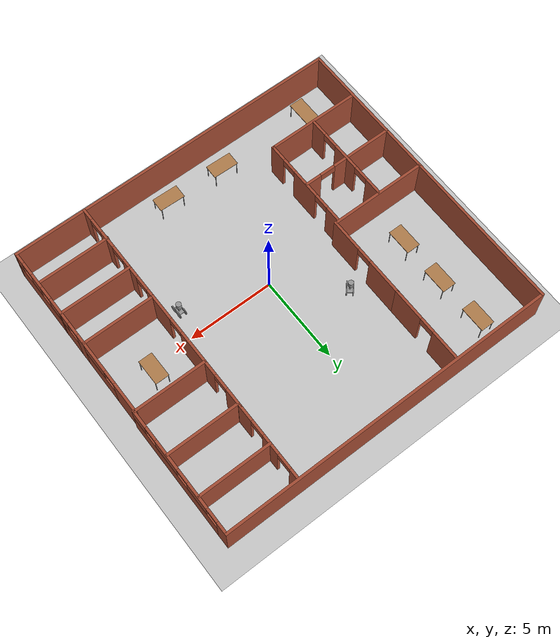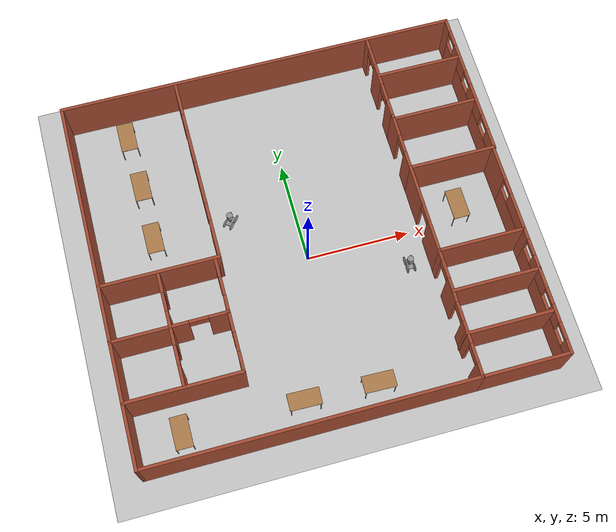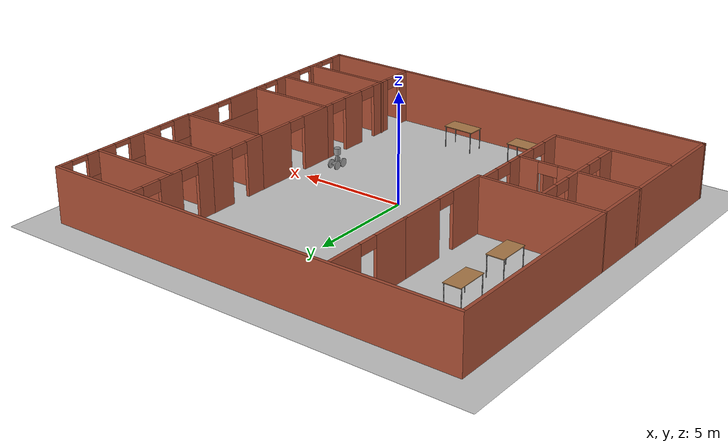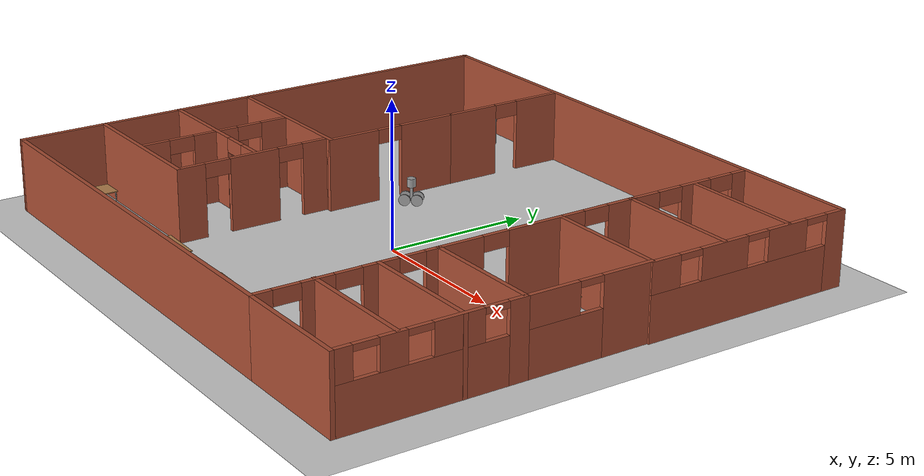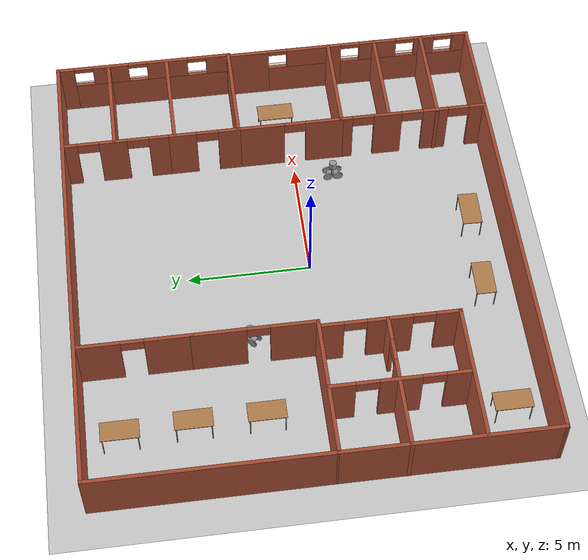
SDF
<sdf version="1.6">
 <world name="default">
  <plugin name="welcome_message" filename="libwelcome_message.so"/>
  <light name="sun" type="directional">
   <pose>0 0 10 0 -0 0</pose>
   <diffuse>0.8 0.8 0.8 1</diffuse>
   <specular>0.2 0.2 0.2 1</specular>
   <attenuation>
    <range>1000</range>
    <constant>0.9</constant>
    <linear>0.01</linear>
    <quadratic>0.001</quadratic>
   </attenuation>
   <direction>-0.5 0.1 -0.9</direction>
  </light>
  <model name="ground_plane">
   <static>1</static>
   <link name="link">
    <collision name="collision">
     <geometry><plane><normal>0 0 1</normal><size>100 100</size></plane></geometry>
     <surface><friction><ode><mu>100</mu><mu2>50</mu2></ode></friction></surface>
    </collision>
    <visual name="visual">
     <cast_shadows>0</cast_shadows>
     <geometry><plane><normal>0 0 1</normal><size>100 100</size></plane></geometry>
     <material>
      <script><uri>file://media/materials/scripts/gazebo.material</uri><name>Gazebo/Grey</name></script>
     </material>
    </visual>
   </link>
  </model>
  <gravity>0 0 -9.8</gravity>
  <magnetic_field>6e-06 2.3e-05 -4.2e-05</magnetic_field>
  <atmosphere type="adiabatic"/>
  <physics name="default_physics" default="0" type="ode">
   <max_step_size>0.001</max_step_size>
   <real_time_factor>1</real_time_factor>
   <real_time_update_rate>1000</real_time_update_rate>
  </physics>
  <scene><ambient>0.4 0.4 0.4 1</ambient><background>0.7 0.7 0.7 1</background><shadows>1</shadows></scene>
  <spherical_coordinates>
   <surface_model>EARTH_WGS84</surface_model>
   <latitude_deg>0</latitude_deg>
   <longitude_deg>0</longitude_deg>
   <elevation>0</elevation>
   <heading_deg>0</heading_deg>
  </spherical_coordinates>
  <model name="model">
   <pose>0.04108 0.71194 0 0 -0 0</pose>
   <link name="Wall_100">
    <pose>5.59529 6.58082 0 0 -0 1.5708</pose>
    <visual name="Wall_100_Visual_0">
     <pose>-1.7592 0 1.25 0 -0 0</pose>
     <geometry><box><size>0.981608 0.15 2.5</size></box></geometry>
     <material>
      <script><uri>file://media/materials/scripts/gazebo.material</uri><name>Gazebo/Bricks</name></script>
      <ambient>1 1 1 1</ambient>
     </material>
     <meta><layer>0</layer></meta>
    </visual>
    <collision name="Wall_100_Collision_0">
     <geometry><box><size>0.981608 0.15 2.5</size></box></geometry>
     <pose>-1.7592 0 1.25 0 -0 0</pose>
    </collision>
    <visual name="Wall_100_Visual_1">
     <pose>0.216608 0 1.25 0 -0 0</pose>
     <geometry><box><size>1.17 0.15 2.5</size></box></geometry>
     <material>
      <script><uri>file://media/materials/scripts/gazebo.material</uri><name>Gazebo/Bricks</name></script>
      <ambient>1 1 1 1</ambient>
     </material>
     <meta><layer>0</layer></meta>
    </visual>
    <collision name="Wall_100_Collision_1">
     <geometry><box><size>1.17 0.15 2.5</size></box></geometry>
     <pose>0.216608 0 1.25 0 -0 0</pose>
    </collision>
    <visual name="Wall_100_Visual_2">
     <pose>1.9758 0 1.25 0 -0 0</pose>
     <geometry><box><size>0.548392 0.15 2.5</size></box></geometry>
     <material>
      <script><uri>file://media/materials/scripts/gazebo.material</uri><name>Gazebo/Bricks</name></script>
      <ambient>1 1 1 1</ambient>
     </material>
     <meta><layer>0</layer></meta>
    </visual>
    <collision name="Wall_100_Collision_2">
     <geometry><box><size>0.548392 0.15 2.5</size></box></geometry>
     <pose>1.9758 0 1.25 0 -0 0</pose>
    </collision>
    <visual name="Wall_100_Visual_3">
     <pose>-0.818392 0 2.25 0 -0 0</pose>
     <geometry><box><size>0.9 0.15 0.5</size></box></geometry>
     <material>
      <script><uri>file://media/materials/scripts/gazebo.material</uri><name>Gazebo/Bricks</name></script>
      <ambient>1 1 1 1</ambient>
     </material>
     <meta><layer>0</layer></meta>
    </visual>
    <collision name="Wall_100_Collision_3">
     <geometry><box><size>0.9 0.15 0.5</size></box></geometry>
     <pose>-0.818392 0 2.25 0 -0 0</pose>
    </collision>
    <visual name="Wall_100_Visual_4">
     <pose>1.25161 0 2.25 0 -0 0</pose>
     <geometry><box><size>0.9 0.15 0.5</size></box></geometry>
     <material>
      <script><uri>file://media/materials/scripts/gazebo.material</uri><name>Gazebo/Bricks</name></script>
      <ambient>1 1 1 1</ambient>
     </material>
     <meta><layer>0</layer></meta>
    </visual>
    <collision name="Wall_100_Collision_4">
     <geometry><box><size>0.9 0.15 0.5</size></box></geometry>
     <pose>1.25161 0 2.25 0 -0 0</pose>
    </collision>
   </link>
   <link name="Wall_102">
    <pose>9.69529 -5.84418 0 0 0 -1.5708</pose>
    <visual name="Wall_102_Visual_0">
     <pose>-2.80184 0 1.25 0 -0 0</pose>
     <geometry><box><size>0.646321 0.15 2.5</size></box></geometry>
     <material>
      <script><uri>file://media/materials/scripts/gazebo.material</uri><name>Gazebo/Bricks</name></script>
      <ambient>0.513726 0.407843 0.482353 1</ambient>
     </material>
     <meta><layer>0</layer></meta>
    </visual>
    <collision name="Wall_102_Collision_0">
     <geometry><box><size>0.646321 0.15 2.5</size></box></geometry>
     <pose>-2.80184 0 1.25 0 -0 0</pose>
    </collision>
    <visual name="Wall_102_Visual_1">
     <pose>0.32316 0 0.75 0 -0 0</pose>
     <geometry><box><size>5.60368 0.15 1.5</size></box></geometry>
     <material>
      <script><uri>file://media/materials/scripts/gazebo.material</uri><name>Gazebo/Bricks</name></script>
      <ambient>0.513726 0.407843 0.482353 1</ambient>
     </material>
     <meta><layer>0</layer></meta>
    </visual>
    <collision name="Wall_102_Collision_1">
     <geometry><box><size>5.60368 0.15 1.5</size></box></geometry>
     <pose>0.32316 0 0.75 0 -0 0</pose>
    </collision>
    <visual name="Wall_102_Visual_2">
     <pose>-0.86558 0 2 0 -0 0</pose>
     <geometry><box><size>1.6262 0.15 1</size></box></geometry>
     <material>
      <script><uri>file://media/materials/scripts/gazebo.material</uri><name>Gazebo/Bricks</name></script>
      <ambient>0.513726 0.407843 0.482353 1</ambient>
     </material>
     <meta><layer>0</layer></meta>
    </visual>
    <collision name="Wall_102_Collision_2">
     <geometry><box><size>1.6262 0.15 1</size></box></geometry>
     <pose>-0.86558 0 2 0 -0 0</pose>
    </collision>
    <visual name="Wall_102_Visual_3">
     <pose>1.186 0 2 0 -0 0</pose>
     <geometry><box><size>0.87697 0.15 1</size></box></geometry>
     <material>
      <script><uri>file://media/materials/scripts/gazebo.material</uri><name>Gazebo/Bricks</name></script>
      <ambient>0.513726 0.407843 0.482353 1</ambient>
     </material>
     <meta><layer>0</layer></meta>
    </visual>
    <collision name="Wall_102_Collision_3">
     <geometry><box><size>0.87697 0.15 1</size></box></geometry>
     <pose>1.186 0 2 0 -0 0</pose>
    </collision>
    <visual name="Wall_102_Visual_4">
     <pose>2.77474 0 2 0 -0 0</pose>
     <geometry><box><size>0.700511 0.15 1</size></box></geometry>
     <material>
      <script><uri>file://media/materials/scripts/gazebo.material</uri><name>Gazebo/Bricks</name></script>
      <ambient>0.513726 0.407843 0.482353 1</ambient>
     </material>
     <meta><layer>0</layer></meta>
    </visual>
    <collision name="Wall_102_Collision_4">
     <geometry><box><size>0.700511 0.15 1</size></box></geometry>
     <pose>2.77474 0 2 0 -0 0</pose>
    </collision>
    <visual name="Wall_102_Visual_5">
     <pose>-2.07868 0 2.4 0 -0 0</pose>
     <geometry><box><size>0.8 0.15 0.2</size></box></geometry>
     <material>
      <script><uri>file://media/materials/scripts/gazebo.material</uri><name>Gazebo/Bricks</name></script>
      <ambient>0.513726 0.407843 0.482353 1</ambient>
     </material>
     <meta><layer>0</layer></meta>
    </visual>
    <collision name="Wall_102_Collision_5">
     <geometry><box><size>0.8 0.15 0.2</size></box></geometry>
     <pose>-2.07868 0 2.4 0 -0 0</pose>
    </collision>
    <visual name="Wall_102_Visual_6">
     <pose>0.347519 0 2.4 0 -0 0</pose>
     <geometry><box><size>0.8 0.15 0.2</size></box></geometry>
     <material>
      <script><uri>file://media/materials/scripts/gazebo.material</uri><name>Gazebo/Bricks</name></script>
      <ambient>0.513726 0.407843 0.482353 1</ambient>
     </material>
     <meta><layer>0</layer></meta>
    </visual>
    <collision name="Wall_102_Collision_6">
     <geometry><box><size>0.8 0.15 0.2</size></box></geometry>
     <pose>0.347519 0 2.4 0 -0 0</pose>
    </collision>
    <visual name="Wall_102_Visual_7">
     <pose>2.02449 0 2.4 0 -0 0</pose>
     <geometry><box><size>0.8 0.15 0.2</size></box></geometry>
     <material>
      <script><uri>file://media/materials/scripts/gazebo.material</uri><name>Gazebo/Bricks</name></script>
      <ambient>0.513726 0.407843 0.482353 1</ambient>
     </material>
     <meta><layer>0</layer></meta>
    </visual>
    <collision name="Wall_102_Collision_7">
     <geometry><box><size>0.8 0.15 0.2</size></box></geometry>
     <pose>2.02449 0 2.4 0 -0 0</pose>
    </collision>
   </link>
   <link name="Wall_103">
    <collision name="Wall_103_Collision">
     <geometry><box><size>4.25 0.15 2.5</size></box></geometry>
     <pose>0 0 1.25 0 -0 0</pose>
    </collision>
    <visual name="Wall_103_Visual">
     <pose>0 0 1.25 0 -0 0</pose>
     <geometry><box><size>4.25 0.15 2.5</size></box></geometry>
     <material>
      <script><uri>file://media/materials/scripts/gazebo.material</uri><name>Gazebo/Bricks</name></script>
      <ambient>0.513726 0.407843 0.482353 1</ambient>
     </material>
     <meta><layer>0</layer></meta>
    </visual>
    <pose>7.64529 -8.89418 0 0 -0 3.14159</pose>
   </link>
   <link name="Wall_105">
    <pose>5.59529 -0.619178 0 0 0 -1.5708</pose>
    <visual name="Wall_105_Visual_0">
     <pose>-1.24513 0 1.25 0 -0 0</pose>
     <geometry><box><size>2.00974 0.15 2.5</size></box></geometry>
     <material>
      <script><uri>file://media/materials/scripts/gazebo.material</uri><name>Gazebo/Bricks</name></script>
      <ambient>1 1 1 1</ambient>
     </material>
     <meta><layer>0</layer></meta>
    </visual>
    <collision name="Wall_105_Collision_0">
     <geometry><box><size>2.00974 0.15 2.5</size></box></geometry>
     <pose>-1.24513 0 1.25 0 -0 0</pose>
    </collision>
    <visual name="Wall_105_Visual_1">
     <pose>1.45487 0 1.25 0 -0 0</pose>
     <geometry><box><size>1.59026 0.15 2.5</size></box></geometry>
     <material>
      <script><uri>file://media/materials/scripts/gazebo.material</uri><name>Gazebo/Bricks</name></script>
      <ambient>1 1 1 1</ambient>
     </material>
     <meta><layer>0</layer></meta>
    </visual>
    <collision name="Wall_105_Collision_1">
     <geometry><box><size>1.59026 0.15 2.5</size></box></geometry>
     <pose>1.45487 0 1.25 0 -0 0</pose>
    </collision>
    <visual name="Wall_105_Visual_2">
     <pose>0.209739 0 2.25 0 -0 0</pose>
     <geometry><box><size>0.9 0.15 0.5</size></box></geometry>
     <material>
      <script><uri>file://media/materials/scripts/gazebo.material</uri><name>Gazebo/Bricks</name></script>
      <ambient>1 1 1 1</ambient>
     </material>
     <meta><layer>0</layer></meta>
    </visual>
    <collision name="Wall_105_Collision_2">
     <geometry><box><size>0.9 0.15 0.5</size></box></geometry>
     <pose>0.209739 0 2.25 0 -0 0</pose>
    </collision>
   </link>
   <link name="Wall_107">
    <collision name="Wall_107_Collision">
     <geometry><box><size>4.25 0.15 2.5</size></box></geometry>
     <pose>0 0 1.25 0 -0 0</pose>
    </collision>
    <visual name="Wall_107_Visual">
     <pose>0 0 1.25 0 -0 0</pose>
     <geometry><box><size>4.25 0.15 2.5</size></box></geometry>
     <material>
      <script><uri>file://media/materials/scripts/gazebo.material</uri><name>Gazebo/Bricks</name></script>
      <ambient>0 0 0.498039 1</ambient>
     </material>
     <meta><layer>0</layer></meta>
    </visual>
    <pose>7.65134 4.2397 0 0 -0 0</pose>
   </link>
   <link name="Wall_109">
    <collision name="Wall_109_Collision">
     <geometry><box><size>4.25 0.15 2.5</size></box></geometry>
     <pose>0 0 1.25 0 -0 0</pose>
    </collision>
    <visual name="Wall_109_Visual">
     <pose>0 0 1.25 0 -0 0</pose>
     <geometry><box><size>4.25 0.15 2.5</size></box></geometry>
     <material>
      <script><uri>file://media/materials/scripts/gazebo.material</uri><name>Gazebo/Bricks</name></script>
      <ambient>0 0 0.498039 1</ambient>
     </material>
     <meta><layer>0</layer></meta>
    </visual>
    <pose>7.65134 6.73379 0 0 -0 0</pose>
   </link>
   <link name="Wall_111">
    <collision name="Wall_111_Collision">
     <geometry><box><size>4.25 0.15 2.5</size></box></geometry>
     <pose>0 0 1.25 0 -0 0</pose>
    </collision>
    <visual name="Wall_111_Visual">
     <pose>0 0 1.25 0 -0 0</pose>
     <geometry><box><size>4.25 0.15 2.5</size></box></geometry>
     <material>
      <script><uri>file://media/materials/scripts/gazebo.material</uri><name>Gazebo/Bricks</name></script>
      <ambient>0 0 0.498039 1</ambient>
     </material>
     <meta><layer>0</layer></meta>
    </visual>
    <pose>7.65134 -4.8114 0 0 -0 0</pose>
   </link>
   <link name="Wall_113">
    <collision name="Wall_113_Collision">
     <geometry><box><size>4.25 0.15 2.5</size></box></geometry>
     <pose>0 0 1.25 0 -0 0</pose>
    </collision>
    <visual name="Wall_113_Visual">
     <pose>0 0 1.25 0 -0 0</pose>
     <geometry><box><size>4.25 0.15 2.5</size></box></geometry>
     <material>
      <script><uri>file://media/materials/scripts/gazebo.material</uri><name>Gazebo/Bricks</name></script>
      <ambient>0 0 0.498039 1</ambient>
     </material>
     <meta><layer>0</layer></meta>
    </visual>
    <pose>7.61112 -6.86299 0 0 -0 0</pose>
   </link>
   <link name="Wall_115">
    <pose>-4.14519 6.56888 0 0 -0 1.5708</pose>
    <visual name="Wall_115_Visual_0">
     <pose>-1.29772 0 1.25 0 -0 0</pose>
     <geometry><box><size>1.90457 0.15 2.5</size></box></geometry>
     <material>
      <script><uri>file://media/materials/scripts/gazebo.material</uri><name>Gazebo/Bricks</name></script>
      <ambient>1 1 1 1</ambient>
     </material>
     <meta><layer>0</layer></meta>
    </visual>
    <collision name="Wall_115_Collision_0">
     <geometry><box><size>1.90457 0.15 2.5</size></box></geometry>
     <pose>-1.29772 0 1.25 0 -0 0</pose>
    </collision>
    <visual name="Wall_115_Visual_1">
     <pose>1.40228 0 1.25 0 -0 0</pose>
     <geometry><box><size>1.69543 0.15 2.5</size></box></geometry>
     <material>
      <script><uri>file://media/materials/scripts/gazebo.material</uri><name>Gazebo/Bricks</name></script>
      <ambient>1 1 1 1</ambient>
     </material>
     <meta><layer>0</layer></meta>
    </visual>
    <collision name="Wall_115_Collision_1">
     <geometry><box><size>1.69543 0.15 2.5</size></box></geometry>
     <pose>1.40228 0 1.25 0 -0 0</pose>
    </collision>
    <visual name="Wall_115_Visual_2">
     <pose>0.104567 0 2.25 0 -0 0</pose>
     <geometry><box><size>0.9 0.15 0.5</size></box></geometry>
     <material>
      <script><uri>file://media/materials/scripts/gazebo.material</uri><name>Gazebo/Bricks</name></script>
      <ambient>1 1 1 1</ambient>
     </material>
     <meta><layer>0</layer></meta>
    </visual>
    <collision name="Wall_115_Collision_2">
     <geometry><box><size>0.9 0.15 0.5</size></box></geometry>
     <pose>0.104567 0 2.25 0 -0 0</pose>
    </collision>
   </link>
   <link name="Wall_117">
    <collision name="Wall_117_Collision">
     <geometry><box><size>5.5 0.15 2.5</size></box></geometry>
     <pose>0 0 1.25 0 -0 0</pose>
    </collision>
    <visual name="Wall_117_Visual">
     <pose>0 0 1.25 0 -0 0</pose>
     <geometry><box><size>5.5 0.15 2.5</size></box></geometry>
     <material>
      <script><uri>file://media/materials/scripts/gazebo.material</uri><name>Gazebo/Bricks</name></script>
      <ambient>1 1 1 1</ambient>
     </material>
     <meta><layer>0</layer></meta>
    </visual>
    <pose>-7.03374 -5.95268 0 0 -0 0</pose>
   </link>
   <link name="Wall_118">
    <pose>-4.35874 -3.27767 0 0 -0 1.5708</pose>
    <visual name="Wall_118_Visual_0">
     <pose>-2.24358 0 1.25 0 -0 0</pose>
     <geometry><box><size>1.01284 0.15 2.5</size></box></geometry>
     <material>
      <script><uri>file://media/materials/scripts/gazebo.material</uri><name>Gazebo/Bricks</name></script>
      <ambient>1 1 1 1</ambient>
     </material>
     <meta><layer>0</layer></meta>
    </visual>
    <collision name="Wall_118_Collision_0">
     <geometry><box><size>1.01284 0.15 2.5</size></box></geometry>
     <pose>-2.24358 0 1.25 0 -0 0</pose>
    </collision>
    <visual name="Wall_118_Visual_1">
     <pose>0.054412 0 1.25 0 -0 0</pose>
     <geometry><box><size>1.78315 0.15 2.5</size></box></geometry>
     <material>
      <script><uri>file://media/materials/scripts/gazebo.material</uri><name>Gazebo/Bricks</name></script>
      <ambient>1 1 1 1</ambient>
     </material>
     <meta><layer>0</layer></meta>
    </visual>
    <collision name="Wall_118_Collision_1">
     <geometry><box><size>1.78315 0.15 2.5</size></box></geometry>
     <pose>0.054412 0 1.25 0 -0 0</pose>
    </collision>
    <visual name="Wall_118_Visual_2">
     <pose>2.29799 0 1.25 0 -0 0</pose>
     <geometry><box><size>0.904013 0.15 2.5</size></box></geometry>
     <material>
      <script><uri>file://media/materials/scripts/gazebo.material</uri><name>Gazebo/Bricks</name></script>
      <ambient>1 1 1 1</ambient>
     </material>
     <meta><layer>0</layer></meta>
    </visual>
    <collision name="Wall_118_Collision_2">
     <geometry><box><size>0.904013 0.15 2.5</size></box></geometry>
     <pose>2.29799 0 1.25 0 -0 0</pose>
    </collision>
    <visual name="Wall_118_Visual_3">
     <pose>-1.28716 0 2.25 0 -0 0</pose>
     <geometry><box><size>0.9 0.15 0.5</size></box></geometry>
     <material>
      <script><uri>file://media/materials/scripts/gazebo.material</uri><name>Gazebo/Bricks</name></script>
      <ambient>1 1 1 1</ambient>
     </material>
     <meta><layer>0</layer></meta>
    </visual>
    <collision name="Wall_118_Collision_3">
     <geometry><box><size>0.9 0.15 0.5</size></box></geometry>
     <pose>-1.28716 0 2.25 0 -0 0</pose>
    </collision>
    <visual name="Wall_118_Visual_4">
     <pose>1.39599 0 2.25 0 -0 0</pose>
     <geometry><box><size>0.9 0.15 0.5</size></box></geometry>
     <material>
      <script><uri>file://media/materials/scripts/gazebo.material</uri><name>Gazebo/Bricks</name></script>
      <ambient>1 1 1 1</ambient>
     </material>
     <meta><layer>0</layer></meta>
    </visual>
    <collision name="Wall_118_Collision_4">
     <geometry><box><size>0.9 0.15 0.5</size></box></geometry>
     <pose>1.39599 0 2.25 0 -0 0</pose>
    </collision>
   </link>
   <link name="Wall_120">
    <pose>-7.08 -3.13074 0 0 -0 0</pose>
    <visual name="Wall_120_Visual_0">
     <pose>-0.925137 0 1.25 0 -0 0</pose>
     <geometry><box><size>3.64973 0.15 2.5</size></box></geometry>
     <material>
      <script><uri>file://media/materials/scripts/gazebo.material</uri><name>Gazebo/Bricks</name></script>
      <ambient>1 1 1 1</ambient>
     </material>
     <meta><layer>0</layer></meta>
    </visual>
    <collision name="Wall_120_Collision_0">
     <geometry><box><size>3.64973 0.15 2.5</size></box></geometry>
     <pose>-0.925137 0 1.25 0 -0 0</pose>
    </collision>
    <visual name="Wall_120_Visual_1">
     <pose>2.27486 0 1.25 0 -0 0</pose>
     <geometry><box><size>0.950274 0.15 2.5</size></box></geometry>
     <material>
      <script><uri>file://media/materials/scripts/gazebo.material</uri><name>Gazebo/Bricks</name></script>
      <ambient>1 1 1 1</ambient>
     </material>
     <meta><layer>0</layer></meta>
    </visual>
    <collision name="Wall_120_Collision_1">
     <geometry><box><size>0.950274 0.15 2.5</size></box></geometry>
     <pose>2.27486 0 1.25 0 -0 0</pose>
    </collision>
    <visual name="Wall_120_Visual_2">
     <pose>1.34973 0 2.25 0 -0 0</pose>
     <geometry><box><size>0.9 0.15 0.5</size></box></geometry>
     <material>
      <script><uri>file://media/materials/scripts/gazebo.material</uri><name>Gazebo/Bricks</name></script>
      <ambient>1 1 1 1</ambient>
     </material>
     <meta><layer>0</layer></meta>
    </visual>
    <collision name="Wall_120_Collision_2">
     <geometry><box><size>0.9 0.15 0.5</size></box></geometry>
     <pose>1.34973 0 2.25 0 -0 0</pose>
    </collision>
   </link>
   <link name="Wall_122">
    <pose>-7.02559 -3.16885 0 0 0 -1.5708</pose>
    <visual name="Wall_122_Visual_0">
     <pose>-2.22045 0 1.25 0 -0 0</pose>
     <geometry><box><size>1.0591 0.15 2.5</size></box></geometry>
     <material>
      <script><uri>file://media/materials/scripts/gazebo.material</uri><name>Gazebo/Bricks</name></script>
      <ambient>1 1 1 1</ambient>
     </material>
     <meta><layer>0</layer></meta>
    </visual>
    <collision name="Wall_122_Collision_0">
     <geometry><box><size>1.0591 0.15 2.5</size></box></geometry>
     <pose>-2.22045 0 1.25 0 -0 0</pose>
    </collision>
    <visual name="Wall_122_Visual_1">
     <pose>0.031281 0 1.25 0 -0 0</pose>
     <geometry><box><size>1.64437 0.15 2.5</size></box></geometry>
     <material>
      <script><uri>file://media/materials/scripts/gazebo.material</uri><name>Gazebo/Bricks</name></script>
      <ambient>1 1 1 1</ambient>
     </material>
     <meta><layer>0</layer></meta>
    </visual>
    <collision name="Wall_122_Collision_1">
     <geometry><box><size>1.64437 0.15 2.5</size></box></geometry>
     <pose>0.031281 0 1.25 0 -0 0</pose>
    </collision>
    <visual name="Wall_122_Visual_2">
     <pose>2.25173 0 1.25 0 -0 0</pose>
     <geometry><box><size>0.996536 0.15 2.5</size></box></geometry>
     <material>
      <script><uri>file://media/materials/scripts/gazebo.material</uri><name>Gazebo/Bricks</name></script>
      <ambient>1 1 1 1</ambient>
     </material>
     <meta><layer>0</layer></meta>
    </visual>
    <collision name="Wall_122_Collision_2">
     <geometry><box><size>0.996536 0.15 2.5</size></box></geometry>
     <pose>2.25173 0 1.25 0 -0 0</pose>
    </collision>
    <visual name="Wall_122_Visual_3">
     <pose>-1.2409 0 2.25 0 -0 0</pose>
     <geometry><box><size>0.9 0.15 0.5</size></box></geometry>
     <material>
      <script><uri>file://media/materials/scripts/gazebo.material</uri><name>Gazebo/Bricks</name></script>
      <ambient>1 1 1 1</ambient>
     </material>
     <meta><layer>0</layer></meta>
    </visual>
    <collision name="Wall_122_Collision_3">
     <geometry><box><size>0.9 0.15 0.5</size></box></geometry>
     <pose>-1.2409 0 2.25 0 -0 0</pose>
    </collision>
    <visual name="Wall_122_Visual_4">
     <pose>1.30346 0 2.25 0 -0 0</pose>
     <geometry><box><size>0.9 0.15 0.5</size></box></geometry>
     <material>
      <script><uri>file://media/materials/scripts/gazebo.material</uri><name>Gazebo/Bricks</name></script>
      <ambient>1 1 1 1</ambient>
     </material>
     <meta><layer>0</layer></meta>
    </visual>
    <collision name="Wall_122_Collision_4">
     <geometry><box><size>0.9 0.15 0.5</size></box></geometry>
     <pose>1.30346 0 2.25 0 -0 0</pose>
    </collision>
   </link>
   <link name="Wall_74">
    <pose>5.59529 2.98082 0 0 0 -1.5708</pose>
    <visual name="Wall_74_Visual_0">
     <pose>-0.916804 0 1.25 0 -0 0</pose>
     <geometry><box><size>1.16639 0.15 2.5</size></box></geometry>
     <material>
      <script><uri>file://media/materials/scripts/gazebo.material</uri><name>Gazebo/Bricks</name></script>
      <ambient>1 1 1 1</ambient>
     </material>
     <meta><layer>0</layer></meta>
    </visual>
    <collision name="Wall_74_Collision_0">
     <geometry><box><size>1.16639 0.15 2.5</size></box></geometry>
     <pose>-0.916804 0 1.25 0 -0 0</pose>
    </collision>
    <visual name="Wall_74_Visual_1">
     <pose>1.0332 0 1.25 0 -0 0</pose>
     <geometry><box><size>0.933608 0.15 2.5</size></box></geometry>
     <material>
      <script><uri>file://media/materials/scripts/gazebo.material</uri><name>Gazebo/Bricks</name></script>
      <ambient>1 1 1 1</ambient>
     </material>
     <meta><layer>0</layer></meta>
    </visual>
    <collision name="Wall_74_Collision_1">
     <geometry><box><size>0.933608 0.15 2.5</size></box></geometry>
     <pose>1.0332 0 1.25 0 -0 0</pose>
    </collision>
    <visual name="Wall_74_Visual_2">
     <pose>0.116392 0 2.25 0 -0 0</pose>
     <geometry><box><size>0.9 0.15 0.5</size></box></geometry>
     <material>
      <script><uri>file://media/materials/scripts/gazebo.material</uri><name>Gazebo/Bricks</name></script>
      <ambient>1 1 1 1</ambient>
     </material>
     <meta><layer>0</layer></meta>
    </visual>
    <collision name="Wall_74_Collision_2">
     <geometry><box><size>0.9 0.15 0.5</size></box></geometry>
     <pose>0.116392 0 2.25 0 -0 0</pose>
    </collision>
   </link>
   <link name="Wall_75">
    <collision name="Wall_75_Collision">
     <geometry><box><size>4.25 0.15 2.5</size></box></geometry>
     <pose>0 0 1.25 0 -0 0</pose>
    </collision>
    <visual name="Wall_75_Visual">
     <pose>0 0 1.25 0 -0 0</pose>
     <geometry><box><size>4.25 0.15 2.5</size></box></geometry>
     <material>
      <script><uri>file://media/materials/scripts/gazebo.material</uri><name>Gazebo/Bricks</name></script>
      <ambient>0 0 0.498039 1</ambient>
     </material>
     <meta><layer>0</layer></meta>
    </visual>
    <pose>7.64529 1.55582 0 0 -0 0</pose>
   </link>
   <link name="Wall_76">
    <pose>9.69529 -0.619178 0 0 0 -1.5708</pose>
    <visual name="Wall_76_Visual_0">
     <pose>-1.34081 0 1.25 0 -0 0</pose>
     <geometry><box><size>1.81838 0.15 2.5</size></box></geometry>
     <material>
      <script><uri>file://media/materials/scripts/gazebo.material</uri><name>Gazebo/Bricks</name></script>
      <ambient>0.513726 0.407843 0.482353 1</ambient>
     </material>
     <meta><layer>0</layer></meta>
    </visual>
    <collision name="Wall_76_Collision_0">
     <geometry><box><size>1.81838 0.15 2.5</size></box></geometry>
     <pose>-1.34081 0 1.25 0 -0 0</pose>
    </collision>
    <visual name="Wall_76_Visual_1">
     <pose>0.909188 0 0.75 0 -0 0</pose>
     <geometry><box><size>2.68162 0.15 1.5</size></box></geometry>
     <material>
      <script><uri>file://media/materials/scripts/gazebo.material</uri><name>Gazebo/Bricks</name></script>
      <ambient>0.513726 0.407843 0.482353 1</ambient>
     </material>
     <meta><layer>0</layer></meta>
    </visual>
    <collision name="Wall_76_Collision_1">
     <geometry><box><size>2.68162 0.15 1.5</size></box></geometry>
     <pose>0.909188 0 0.75 0 -0 0</pose>
    </collision>
    <visual name="Wall_76_Visual_2">
     <pose>1.30919 0 2 0 -0 0</pose>
     <geometry><box><size>1.88162 0.15 1</size></box></geometry>
     <material>
      <script><uri>file://media/materials/scripts/gazebo.material</uri><name>Gazebo/Bricks</name></script>
      <ambient>0.513726 0.407843 0.482353 1</ambient>
     </material>
     <meta><layer>0</layer></meta>
    </visual>
    <collision name="Wall_76_Collision_2">
     <geometry><box><size>1.88162 0.15 1</size></box></geometry>
     <pose>1.30919 0 2 0 -0 0</pose>
    </collision>
    <visual name="Wall_76_Visual_3">
     <pose>-0.031624 0 2.4 0 -0 0</pose>
     <geometry><box><size>0.8 0.15 0.2</size></box></geometry>
     <material>
      <script><uri>file://media/materials/scripts/gazebo.material</uri><name>Gazebo/Bricks</name></script>
      <ambient>0.513726 0.407843 0.482353 1</ambient>
     </material>
     <meta><layer>0</layer></meta>
    </visual>
    <collision name="Wall_76_Collision_3">
     <geometry><box><size>0.8 0.15 0.2</size></box></geometry>
     <pose>-0.031624 0 2.4 0 -0 0</pose>
    </collision>
   </link>
   <link name="Wall_77">
    <collision name="Wall_77_Collision">
     <geometry><box><size>4.25 0.15 2.5</size></box></geometry>
     <pose>0 0 1.25 0 -0 0</pose>
    </collision>
    <visual name="Wall_77_Visual">
     <pose>0 0 1.25 0 -0 0</pose>
     <geometry><box><size>4.25 0.15 2.5</size></box></geometry>
     <material>
      <script><uri>file://media/materials/scripts/gazebo.material</uri><name>Gazebo/Bricks</name></script>
      <ambient>0 0 0.498039 1</ambient>
     </material>
     <meta><layer>0</layer></meta>
    </visual>
    <pose>7.64529 -2.79418 0 0 -0 3.14159</pose>
   </link>
   <link name="Wall_78">
    <pose>5.59529 -5.84418 0 0 0 -1.5708</pose>
    <visual name="Wall_78_Visual_0">
     <pose>-2.84695 0 1.25 0 -0 0</pose>
     <geometry><box><size>0.556094 0.15 2.5</size></box></geometry>
     <material>
      <script><uri>file://media/materials/scripts/gazebo.material</uri><name>Gazebo/Bricks</name></script>
      <ambient>1 1 1 1</ambient>
     </material>
     <meta><layer>0</layer></meta>
    </visual>
    <collision name="Wall_78_Collision_0">
     <geometry><box><size>0.556094 0.15 2.5</size></box></geometry>
     <pose>-2.84695 0 1.25 0 -0 0</pose>
    </collision>
    <visual name="Wall_78_Visual_1">
     <pose>-1.073 0 1.25 0 -0 0</pose>
     <geometry><box><size>1.19181 0.15 2.5</size></box></geometry>
     <material>
      <script><uri>file://media/materials/scripts/gazebo.material</uri><name>Gazebo/Bricks</name></script>
      <ambient>1 1 1 1</ambient>
     </material>
     <meta><layer>0</layer></meta>
    </visual>
    <collision name="Wall_78_Collision_1">
     <geometry><box><size>1.19181 0.15 2.5</size></box></geometry>
     <pose>-1.073 0 1.25 0 -0 0</pose>
    </collision>
    <visual name="Wall_78_Visual_2">
     <pose>0.95847 0 1.25 0 -0 0</pose>
     <geometry><box><size>1.07113 0.15 2.5</size></box></geometry>
     <material>
      <script><uri>file://media/materials/scripts/gazebo.material</uri><name>Gazebo/Bricks</name></script>
      <ambient>1 1 1 1</ambient>
     </material>
     <meta><layer>0</layer></meta>
    </visual>
    <collision name="Wall_78_Collision_2">
     <geometry><box><size>1.07113 0.15 2.5</size></box></geometry>
     <pose>0.95847 0 1.25 0 -0 0</pose>
    </collision>
    <visual name="Wall_78_Visual_3">
     <pose>2.75952 0 1.25 0 -0 0</pose>
     <geometry><box><size>0.730965 0.15 2.5</size></box></geometry>
     <material>
      <script><uri>file://media/materials/scripts/gazebo.material</uri><name>Gazebo/Bricks</name></script>
      <ambient>1 1 1 1</ambient>
     </material>
     <meta><layer>0</layer></meta>
    </visual>
    <collision name="Wall_78_Collision_3">
     <geometry><box><size>0.730965 0.15 2.5</size></box></geometry>
     <pose>2.75952 0 1.25 0 -0 0</pose>
    </collision>
    <visual name="Wall_78_Visual_4">
     <pose>-2.11891 0 2.25 0 -0 0</pose>
     <geometry><box><size>0.9 0.15 0.5</size></box></geometry>
     <material>
      <script><uri>file://media/materials/scripts/gazebo.material</uri><name>Gazebo/Bricks</name></script>
      <ambient>1 1 1 1</ambient>
     </material>
     <meta><layer>0</layer></meta>
    </visual>
    <collision name="Wall_78_Collision_4">
     <geometry><box><size>0.9 0.15 0.5</size></box></geometry>
     <pose>-2.11891 0 2.25 0 -0 0</pose>
    </collision>
    <visual name="Wall_78_Visual_5">
     <pose>-0.027095 0 2.25 0 -0 0</pose>
     <geometry><box><size>0.9 0.15 0.5</size></box></geometry>
     <material>
      <script><uri>file://media/materials/scripts/gazebo.material</uri><name>Gazebo/Bricks</name></script>
      <ambient>1 1 1 1</ambient>
     </material>
     <meta><layer>0</layer></meta>
    </visual>
    <collision name="Wall_78_Collision_5">
     <geometry><box><size>0.9 0.15 0.5</size></box></geometry>
     <pose>-0.027095 0 2.25 0 -0 0</pose>
    </collision>
    <visual name="Wall_78_Visual_6">
     <pose>1.94403 0 2.25 0 -0 0</pose>
     <geometry><box><size>0.9 0.15 0.5</size></box></geometry>
     <material>
      <script><uri>file://media/materials/scripts/gazebo.material</uri><name>Gazebo/Bricks</name></script>
      <ambient>1 1 1 1</ambient>
     </material>
     <meta><layer>0</layer></meta>
    </visual>
    <collision name="Wall_78_Collision_6">
     <geometry><box><size>0.9 0.15 0.5</size></box></geometry>
     <pose>1.94403 0 2.25 0 -0 0</pose>
    </collision>
   </link>
   <link name="Wall_79">
    <collision name="Wall_79_Collision">
     <geometry><box><size>15.5 0.15 2.5</size></box></geometry>
     <pose>0 0 1.25 0 -0 0</pose>
    </collision>
    <visual name="Wall_79_Visual">
     <pose>0 0 1.25 0 -0 0</pose>
     <geometry><box><size>15.5 0.15 2.5</size></box></geometry>
     <material>
      <script><uri>file://media/materials/scripts/gazebo.material</uri><name>Gazebo/Bricks</name></script>
      <ambient>0.513726 0.407843 0.482353 1</ambient>
     </material>
     <meta><layer>0</layer></meta>
    </visual>
    <pose>-2.07971 -8.89418 0 0 -0 3.14159</pose>
   </link>
   <link name="Wall_80">
    <collision name="Wall_80_Collision">
     <geometry><box><size>8.58806 0.15 2.5</size></box></geometry>
     <pose>0 0 1.25 0 -0 0</pose>
    </collision>
    <visual name="Wall_80_Visual">
     <pose>0 0 1.25 0 -0 0</pose>
     <geometry><box><size>8.58806 0.15 2.5</size></box></geometry>
     <material>
      <script><uri>file://media/materials/scripts/gazebo.material</uri><name>Gazebo/Bricks</name></script>
      <ambient>0.498039 0.396078 0.466667 1</ambient>
     </material>
     <meta><layer>0</layer></meta>
    </visual>
    <pose>-9.74995 -4.67515 0 0 -0 1.56967</pose>
   </link>
   <link name="Wall_89">
    <collision name="Wall_89_Collision">
     <geometry><box><size>5.75 0.15 2.5</size></box></geometry>
     <pose>0 0 1.25 0 -0 0</pose>
    </collision>
    <visual name="Wall_89_Visual">
     <pose>0 0 1.25 0 -0 0</pose>
     <geometry><box><size>5.75 0.15 2.5</size></box></geometry>
     <material>
      <script><uri>file://media/materials/scripts/gazebo.material</uri><name>Gazebo/Bricks</name></script>
      <ambient>1 1 1 1</ambient>
     </material>
     <meta><layer>0</layer></meta>
    </visual>
    <pose>-6.94519 -0.456125 0 0 -0 0</pose>
   </link>
   <link name="Wall_90">
    <pose>-4.14519 1.96887 0 0 -0 1.5708</pose>
    <visual name="Wall_90_Visual_0">
     <pose>-1.53934 0 1.25 0 -0 0</pose>
     <geometry><box><size>1.92131 0.15 2.5</size></box></geometry>
     <material>
      <script><uri>file://media/materials/scripts/gazebo.material</uri><name>Gazebo/Bricks</name></script>
      <ambient>1 1 1 1</ambient>
     </material>
     <meta><layer>0</layer></meta>
    </visual>
    <collision name="Wall_90_Collision_0">
     <geometry><box><size>1.92131 0.15 2.5</size></box></geometry>
     <pose>-1.53934 0 1.25 0 -0 0</pose>
    </collision>
    <visual name="Wall_90_Visual_1">
     <pose>1.41065 0 1.25 0 -0 0</pose>
     <geometry><box><size>2.17869 0.15 2.5</size></box></geometry>
     <material>
      <script><uri>file://media/materials/scripts/gazebo.material</uri><name>Gazebo/Bricks</name></script>
      <ambient>1 1 1 1</ambient>
     </material>
     <meta><layer>0</layer></meta>
    </visual>
    <collision name="Wall_90_Collision_1">
     <geometry><box><size>2.17869 0.15 2.5</size></box></geometry>
     <pose>1.41065 0 1.25 0 -0 0</pose>
    </collision>
    <visual name="Wall_90_Visual_2">
     <pose>-0.12869 0 2.25 0 -0 0</pose>
     <geometry><box><size>0.9 0.15 0.5</size></box></geometry>
     <material>
      <script><uri>file://media/materials/scripts/gazebo.material</uri><name>Gazebo/Bricks</name></script>
      <ambient>1 1 1 1</ambient>
     </material>
     <meta><layer>0</layer></meta>
    </visual>
    <collision name="Wall_90_Collision_2">
     <geometry><box><size>0.9 0.15 0.5</size></box></geometry>
     <pose>-0.12869 0 2.25 0 -0 0</pose>
    </collision>
   </link>
   <link name="Wall_93">
    <collision name="Wall_93_Collision">
     <geometry><box><size>9.5 0.15 2.5</size></box></geometry>
     <pose>0 0 1.25 0 -0 0</pose>
    </collision>
    <visual name="Wall_93_Visual">
     <pose>0 0 1.25 0 -0 0</pose>
     <geometry><box><size>9.5 0.15 2.5</size></box></geometry>
     <material>
      <script><uri>file://media/materials/scripts/gazebo.material</uri><name>Gazebo/Bricks</name></script>
      <ambient>0.513726 0.407843 0.482353 1</ambient>
     </material>
     <meta><layer>0</layer></meta>
    </visual>
    <pose>-9.7451 4.21907 0 0 -0 1.57078</pose>
   </link>
   <link name="Wall_94">
    <collision name="Wall_94_Collision">
     <geometry><box><size>19.65 0.15 2.5</size></box></geometry>
     <pose>0 0 1.25 0 -0 0</pose>
    </collision>
    <visual name="Wall_94_Visual">
     <pose>0 0 1.25 0 -0 0</pose>
     <geometry><box><size>19.65 0.15 2.5</size></box></geometry>
     <material>
      <script><uri>file://media/materials/scripts/gazebo.material</uri><name>Gazebo/Bricks</name></script>
      <ambient>0.513726 0.407843 0.482353 1</ambient>
     </material>
     <meta><layer>0</layer></meta>
    </visual>
    <pose>0.004996 8.89426 0 0 -0 0</pose>
   </link>
   <link name="Wall_97">
    <pose>9.755 5.21926 0 0 0 -1.5708</pose>
    <visual name="Wall_97_Visual_0">
     <pose>-3.37008 0 1.25 0 -0 0</pose>
     <geometry><box><size>0.759832 0.15 2.5</size></box></geometry>
     <material>
      <script><uri>file://media/materials/scripts/gazebo.material</uri><name>Gazebo/Bricks</name></script>
      <ambient>0.513726 0.407843 0.482353 1</ambient>
     </material>
     <meta><layer>0</layer></meta>
    </visual>
    <collision name="Wall_97_Collision_0">
     <geometry><box><size>0.759832 0.15 2.5</size></box></geometry>
     <pose>-3.37008 0 1.25 0 -0 0</pose>
    </collision>
    <visual name="Wall_97_Visual_1">
     <pose>0.379916 0 0.75 0 -0 0</pose>
     <geometry><box><size>6.74017 0.15 1.5</size></box></geometry>
     <material>
      <script><uri>file://media/materials/scripts/gazebo.material</uri><name>Gazebo/Bricks</name></script>
      <ambient>0.513726 0.407843 0.482353 1</ambient>
     </material>
     <meta><layer>0</layer></meta>
    </visual>
    <collision name="Wall_97_Collision_1">
     <geometry><box><size>6.74017 0.15 1.5</size></box></geometry>
     <pose>0.379916 0 0.75 0 -0 0</pose>
    </collision>
    <visual name="Wall_97_Visual_2">
     <pose>-1.42867 0 2 0 -0 0</pose>
     <geometry><box><size>1.523 0.15 1</size></box></geometry>
     <material>
      <script><uri>file://media/materials/scripts/gazebo.material</uri><name>Gazebo/Bricks</name></script>
      <ambient>0.513726 0.407843 0.482353 1</ambient>
     </material>
     <meta><layer>0</layer></meta>
    </visual>
    <collision name="Wall_97_Collision_2">
     <geometry><box><size>1.523 0.15 1</size></box></geometry>
     <pose>-1.42867 0 2 0 -0 0</pose>
    </collision>
    <visual name="Wall_97_Visual_3">
     <pose>1.00933 0 2 0 -0 0</pose>
     <geometry><box><size>1.753 0.15 1</size></box></geometry>
     <material>
      <script><uri>file://media/materials/scripts/gazebo.material</uri><name>Gazebo/Bricks</name></script>
      <ambient>0.513726 0.407843 0.482353 1</ambient>
     </material>
     <meta><layer>0</layer></meta>
    </visual>
    <collision name="Wall_97_Collision_3">
     <geometry><box><size>1.753 0.15 1</size></box></geometry>
     <pose>1.00933 0 2 0 -0 0</pose>
    </collision>
    <visual name="Wall_97_Visual_4">
     <pose>3.21792 0 2 0 -0 0</pose>
     <geometry><box><size>1.06417 0.15 1</size></box></geometry>
     <material>
      <script><uri>file://media/materials/scripts/gazebo.material</uri><name>Gazebo/Bricks</name></script>
      <ambient>0.513726 0.407843 0.482353 1</ambient>
     </material>
     <meta><layer>0</layer></meta>
    </visual>
    <collision name="Wall_97_Collision_4">
     <geometry><box><size>1.06417 0.15 1</size></box></geometry>
     <pose>3.21792 0 2 0 -0 0</pose>
    </collision>
    <visual name="Wall_97_Visual_5">
     <pose>-2.59017 0 2.4 0 -0 0</pose>
     <geometry><box><size>0.8 0.15 0.2</size></box></geometry>
     <material>
      <script><uri>file://media/materials/scripts/gazebo.material</uri><name>Gazebo/Bricks</name></script>
      <ambient>0.513726 0.407843 0.482353 1</ambient>
     </material>
     <meta><layer>0</layer></meta>
    </visual>
    <collision name="Wall_97_Collision_5">
     <geometry><box><size>0.8 0.15 0.2</size></box></geometry>
     <pose>-2.59017 0 2.4 0 -0 0</pose>
    </collision>
    <visual name="Wall_97_Visual_6">
     <pose>-0.267167 0 2.4 0 -0 0</pose>
     <geometry><box><size>0.8 0.15 0.2</size></box></geometry>
     <material>
      <script><uri>file://media/materials/scripts/gazebo.material</uri><name>Gazebo/Bricks</name></script>
      <ambient>0.513726 0.407843 0.482353 1</ambient>
     </material>
     <meta><layer>0</layer></meta>
    </visual>
    <collision name="Wall_97_Collision_6">
     <geometry><box><size>0.8 0.15 0.2</size></box></geometry>
     <pose>-0.267167 0 2.4 0 -0 0</pose>
    </collision>
    <visual name="Wall_97_Visual_7">
     <pose>2.28583 0 2.4 0 -0 0</pose>
     <geometry><box><size>0.8 0.15 0.2</size></box></geometry>
     <material>
      <script><uri>file://media/materials/scripts/gazebo.material</uri><name>Gazebo/Bricks</name></script>
      <ambient>0.513726 0.407843 0.482353 1</ambient>
     </material>
     <meta><layer>0</layer></meta>
    </visual>
    <collision name="Wall_97_Collision_7">
     <geometry><box><size>0.8 0.15 0.2</size></box></geometry>
     <pose>2.28583 0 2.4 0 -0 0</pose>
    </collision>
   </link>
   <static>1</static>
  </model>
  <model name="table">
   <static>1</static>
   <link name="link">
    <collision name="surface">
     <pose>0 0 1 0 -0 0</pose>
     <geometry><box><size>1.5 0.8 0.03</size></box></geometry>
     <surface><friction><ode><mu>0.6</mu><mu2>0.6</mu2></ode></friction></surface>
    </collision>
    <visual name="visual1">
     <pose>0 0 1 0 -0 0</pose>
     <geometry><box><size>1.5 0.8 0.03</size></box></geometry>
     <material>
      <script><uri>file://media/materials/scripts/gazebo.material</uri><name>Gazebo/Wood</name></script>
     </material>
    </visual>
    <collision name="front_left_leg">
     <pose>0.68 0.38 0.5 0 -0 0</pose>
     <geometry><cylinder><radius>0.02</radius><length>1</length></cylinder></geometry>
    </collision>
    <visual name="front_left_leg">
     <pose>0.68 0.38 0.5 0 -0 0</pose>
     <geometry><cylinder><radius>0.02</radius><length>1</length></cylinder></geometry>
     <material>
      <script><uri>file://media/materials/scripts/gazebo.material</uri><name>Gazebo/Grey</name></script>
     </material>
    </visual>
    <collision name="front_right_leg">
     <pose>0.68 -0.38 0.5 0 -0 0</pose>
     <geometry><cylinder><radius>0.02</radius><length>1</length></cylinder></geometry>
    </collision>
    <visual name="front_right_leg">
     <pose>0.68 -0.38 0.5 0 -0 0</pose>
     <geometry><cylinder><radius>0.02</radius><length>1</length></cylinder></geometry>
     <material>
      <script><uri>file://media/materials/scripts/gazebo.material</uri><name>Gazebo/Grey</name></script>
     </material>
    </visual>
    <collision name="back_right_leg">
     <pose>-0.68 -0.38 0.5 0 -0 0</pose>
     <geometry><cylinder><radius>0.02</radius><length>1</length></cylinder></geometry>
    </collision>
    <visual name="back_right_leg">
     <pose>-0.68 -0.38 0.5 0 -0 0</pose>
     <geometry><cylinder><radius>0.02</radius><length>1</length></cylinder></geometry>
     <material>
      <script><uri>file://media/materials/scripts/gazebo.material</uri><name>Gazebo/Grey</name></script>
     </material>
    </visual>
    <collision name="back_left_leg">
     <pose>-0.68 0.38 0.5 0 -0 0</pose>
     <geometry><cylinder><radius>0.02</radius><length>1</length></cylinder></geometry>
    </collision>
    <visual name="back_left_leg">
     <pose>-0.68 0.38 0.5 0 -0 0</pose>
     <geometry><cylinder><radius>0.02</radius><length>1</length></cylinder></geometry>
     <material>
      <script><uri>file://media/materials/scripts/gazebo.material</uri><name>Gazebo/Grey</name></script>
     </material>
    </visual>
   </link>
   <pose>-2.00691 -6.77014 0 0 0 -0.026226</pose>
  </model>
  <model name="table_clone">
   <static>1</static>
   <link name="link">
    <collision name="surface">
     <pose>0 0 1 0 -0 0</pose>
     <geometry><box><size>1.5 0.8 0.03</size></box></geometry>
     <surface><friction><ode><mu>0.6</mu><mu2>0.6</mu2></ode></friction></surface>
    </collision>
    <visual name="visual1">
     <pose>0 0 1 0 -0 0</pose>
     <geometry><box><size>1.5 0.8 0.03</size></box></geometry>
     <material>
      <script><uri>file://media/materials/scripts/gazebo.material</uri><name>Gazebo/Wood</name></script>
     </material>
    </visual>
    <collision name="front_left_leg">
     <pose>0.68 0.38 0.5 0 -0 0</pose>
     <geometry><cylinder><radius>0.02</radius><length>1</length></cylinder></geometry>
    </collision>
    <visual name="front_left_leg">
     <pose>0.68 0.38 0.5 0 -0 0</pose>
     <geometry><cylinder><radius>0.02</radius><length>1</length></cylinder></geometry>
     <material>
      <script><uri>file://media/materials/scripts/gazebo.material</uri><name>Gazebo/Grey</name></script>
     </material>
    </visual>
    <collision name="front_right_leg">
     <pose>0.68 -0.38 0.5 0 -0 0</pose>
     <geometry><cylinder><radius>0.02</radius><length>1</length></cylinder></geometry>
    </collision>
    <visual name="front_right_leg">
     <pose>0.68 -0.38 0.5 0 -0 0</pose>
     <geometry><cylinder><radius>0.02</radius><length>1</length></cylinder></geometry>
     <material>
      <script><uri>file://media/materials/scripts/gazebo.material</uri><name>Gazebo/Grey</name></script>
     </material>
    </visual>
    <collision name="back_right_leg">
     <pose>-0.68 -0.38 0.5 0 -0 0</pose>
     <geometry><cylinder><radius>0.02</radius><length>1</length></cylinder></geometry>
    </collision>
    <visual name="back_right_leg">
     <pose>-0.68 -0.38 0.5 0 -0 0</pose>
     <geometry><cylinder><radius>0.02</radius><length>1</length></cylinder></geometry>
     <material>
      <script><uri>file://media/materials/scripts/gazebo.material</uri><name>Gazebo/Grey</name></script>
     </material>
    </visual>
    <collision name="back_left_leg">
     <pose>-0.68 0.38 0.5 0 -0 0</pose>
     <geometry><cylinder><radius>0.02</radius><length>1</length></cylinder></geometry>
    </collision>
    <visual name="back_left_leg">
     <pose>-0.68 0.38 0.5 0 -0 0</pose>
     <geometry><cylinder><radius>0.02</radius><length>1</length></cylinder></geometry>
     <material>
      <script><uri>file://media/materials/scripts/gazebo.material</uri><name>Gazebo/Grey</name></script>
     </material>
    </visual>
   </link>
   <pose>7.5802 0.509102 0 0 -0 1.57261</pose>
  </model>
  <model name="table_clone_0">
   <static>1</static>
   <link name="link">
    <collision name="surface">
     <pose>0 0 1 0 -0 0</pose>
     <geometry><box><size>1.5 0.8 0.03</size></box></geometry>
     <surface><friction><ode><mu>0.6</mu><mu2>0.6</mu2></ode></friction></surface>
    </collision>
    <visual name="visual1">
     <pose>0 0 1 0 -0 0</pose>
     <geometry><box><size>1.5 0.8 0.03</size></box></geometry>
     <material>
      <script><uri>file://media/materials/scripts/gazebo.material</uri><name>Gazebo/Wood</name></script>
     </material>
    </visual>
    <collision name="front_left_leg">
     <pose>0.68 0.38 0.5 0 -0 0</pose>
     <geometry><cylinder><radius>0.02</radius><length>1</length></cylinder></geometry>
    </collision>
    <visual name="front_left_leg">
     <pose>0.68 0.38 0.5 0 -0 0</pose>
     <geometry><cylinder><radius>0.02</radius><length>1</length></cylinder></geometry>
     <material>
      <script><uri>file://media/materials/scripts/gazebo.material</uri><name>Gazebo/Grey</name></script>
     </material>
    </visual>
    <collision name="front_right_leg">
     <pose>0.68 -0.38 0.5 0 -0 0</pose>
     <geometry><cylinder><radius>0.02</radius><length>1</length></cylinder></geometry>
    </collision>
    <visual name="front_right_leg">
     <pose>0.68 -0.38 0.5 0 -0 0</pose>
     <geometry><cylinder><radius>0.02</radius><length>1</length></cylinder></geometry>
     <material>
      <script><uri>file://media/materials/scripts/gazebo.material</uri><name>Gazebo/Grey</name></script>
     </material>
    </visual>
    <collision name="back_right_leg">
     <pose>-0.68 -0.38 0.5 0 -0 0</pose>
     <geometry><cylinder><radius>0.02</radius><length>1</length></cylinder></geometry>
    </collision>
    <visual name="back_right_leg">
     <pose>-0.68 -0.38 0.5 0 -0 0</pose>
     <geometry><cylinder><radius>0.02</radius><length>1</length></cylinder></geometry>
     <material>
      <script><uri>file://media/materials/scripts/gazebo.material</uri><name>Gazebo/Grey</name></script>
     </material>
    </visual>
    <collision name="back_left_leg">
     <pose>-0.68 0.38 0.5 0 -0 0</pose>
     <geometry><cylinder><radius>0.02</radius><length>1</length></cylinder></geometry>
    </collision>
    <visual name="back_left_leg">
     <pose>-0.68 0.38 0.5 0 -0 0</pose>
     <geometry><cylinder><radius>0.02</radius><length>1</length></cylinder></geometry>
     <material>
      <script><uri>file://media/materials/scripts/gazebo.material</uri><name>Gazebo/Grey</name></script>
     </material>
    </visual>
   </link>
   <pose>-7.6186 -6.77238 0 0 0 -1.56936</pose>
  </model>
  <model name="table_clone_1">
   <static>1</static>
   <link name="link">
    <collision name="surface">
     <pose>0 0 1 0 -0 0</pose>
     <geometry><box><size>1.5 0.8 0.03</size></box></geometry>
     <surface><friction><ode><mu>0.6</mu><mu2>0.6</mu2></ode></friction></surface>
    </collision>
    <visual name="visual1">
     <pose>0 0 1 0 -0 0</pose>
     <geometry><box><size>1.5 0.8 0.03</size></box></geometry>
     <material>
      <script><uri>file://media/materials/scripts/gazebo.material</uri><name>Gazebo/Wood</name></script>
     </material>
    </visual>
    <collision name="front_left_leg">
     <pose>0.68 0.38 0.5 0 -0 0</pose>
     <geometry><cylinder><radius>0.02</radius><length>1</length></cylinder></geometry>
    </collision>
    <visual name="front_left_leg">
     <pose>0.68 0.38 0.5 0 -0 0</pose>
     <geometry><cylinder><radius>0.02</radius><length>1</length></cylinder></geometry>
     <material>
      <script><uri>file://media/materials/scripts/gazebo.material</uri><name>Gazebo/Grey</name></script>
     </material>
    </visual>
    <collision name="front_right_leg">
     <pose>0.68 -0.38 0.5 0 -0 0</pose>
     <geometry><cylinder><radius>0.02</radius><length>1</length></cylinder></geometry>
    </collision>
    <visual name="front_right_leg">
     <pose>0.68 -0.38 0.5 0 -0 0</pose>
     <geometry><cylinder><radius>0.02</radius><length>1</length></cylinder></geometry>
     <material>
      <script><uri>file://media/materials/scripts/gazebo.material</uri><name>Gazebo/Grey</name></script>
     </material>
    </visual>
    <collision name="back_right_leg">
     <pose>-0.68 -0.38 0.5 0 -0 0</pose>
     <geometry><cylinder><radius>0.02</radius><length>1</length></cylinder></geometry>
    </collision>
    <visual name="back_right_leg">
     <pose>-0.68 -0.38 0.5 0 -0 0</pose>
     <geometry><cylinder><radius>0.02</radius><length>1</length></cylinder></geometry>
     <material>
      <script><uri>file://media/materials/scripts/gazebo.material</uri><name>Gazebo/Grey</name></script>
     </material>
    </visual>
    <collision name="back_left_leg">
     <pose>-0.68 0.38 0.5 0 -0 0</pose>
     <geometry><cylinder><radius>0.02</radius><length>1</length></cylinder></geometry>
    </collision>
    <visual name="back_left_leg">
     <pose>-0.68 0.38 0.5 0 -0 0</pose>
     <geometry><cylinder><radius>0.02</radius><length>1</length></cylinder></geometry>
     <material>
      <script><uri>file://media/materials/scripts/gazebo.material</uri><name>Gazebo/Grey</name></script>
     </material>
    </visual>
   </link>
   <pose>-7.01291 8.17807 0 0 0 -1.56936</pose>
  </model>
  <model name="table_clone_2">
   <static>1</static>
   <link name="link">
    <collision name="surface">
     <pose>0 0 1 0 -0 0</pose>
     <geometry><box><size>1.5 0.8 0.03</size></box></geometry>
     <surface><friction><ode><mu>0.6</mu><mu2>0.6</mu2></ode></friction></surface>
    </collision>
    <visual name="visual1">
     <pose>0 0 1 0 -0 0</pose>
     <geometry><box><size>1.5 0.8 0.03</size></box></geometry>
     <material>
      <script><uri>file://media/materials/scripts/gazebo.material</uri><name>Gazebo/Wood</name></script>
     </material>
    </visual>
    <collision name="front_left_leg">
     <pose>0.68 0.38 0.5 0 -0 0</pose>
     <geometry><cylinder><radius>0.02</radius><length>1</length></cylinder></geometry>
    </collision>
    <visual name="front_left_leg">
     <pose>0.68 0.38 0.5 0 -0 0</pose>
     <geometry><cylinder><radius>0.02</radius><length>1</length></cylinder></geometry>
     <material>
      <script><uri>file://media/materials/scripts/gazebo.material</uri><name>Gazebo/Grey</name></script>
     </material>
    </visual>
    <collision name="front_right_leg">
     <pose>0.68 -0.38 0.5 0 -0 0</pose>
     <geometry><cylinder><radius>0.02</radius><length>1</length></cylinder></geometry>
    </collision>
    <visual name="front_right_leg">
     <pose>0.68 -0.38 0.5 0 -0 0</pose>
     <geometry><cylinder><radius>0.02</radius><length>1</length></cylinder></geometry>
     <material>
      <script><uri>file://media/materials/scripts/gazebo.material</uri><name>Gazebo/Grey</name></script>
     </material>
    </visual>
    <collision name="back_right_leg">
     <pose>-0.68 -0.38 0.5 0 -0 0</pose>
     <geometry><cylinder><radius>0.02</radius><length>1</length></cylinder></geometry>
    </collision>
    <visual name="back_right_leg">
     <pose>-0.68 -0.38 0.5 0 -0 0</pose>
     <geometry><cylinder><radius>0.02</radius><length>1</length></cylinder></geometry>
     <material>
      <script><uri>file://media/materials/scripts/gazebo.material</uri><name>Gazebo/Grey</name></script>
     </material>
    </visual>
    <collision name="back_left_leg">
     <pose>-0.68 0.38 0.5 0 -0 0</pose>
     <geometry><cylinder><radius>0.02</radius><length>1</length></cylinder></geometry>
    </collision>
    <visual name="back_left_leg">
     <pose>-0.68 0.38 0.5 0 -0 0</pose>
     <geometry><cylinder><radius>0.02</radius><length>1</length></cylinder></geometry>
     <material>
      <script><uri>file://media/materials/scripts/gazebo.material</uri><name>Gazebo/Grey</name></script>
     </material>
    </visual>
   </link>
   <pose>-6.89144 5.3803 0 0 0 -1.56936</pose>
  </model>
  <model name="table_clone_3">
   <static>1</static>
   <link name="link">
    <collision name="surface">
     <pose>0 0 1 0 -0 0</pose>
     <geometry><box><size>1.5 0.8 0.03</size></box></geometry>
     <surface><friction><ode><mu>0.6</mu><mu2>0.6</mu2></ode></friction></surface>
    </collision>
    <visual name="visual1">
     <pose>0 0 1 0 -0 0</pose>
     <geometry><box><size>1.5 0.8 0.03</size></box></geometry>
     <material>
      <script><uri>file://media/materials/scripts/gazebo.material</uri><name>Gazebo/Wood</name></script>
     </material>
    </visual>
    <collision name="front_left_leg">
     <pose>0.68 0.38 0.5 0 -0 0</pose>
     <geometry><cylinder><radius>0.02</radius><length>1</length></cylinder></geometry>
    </collision>
    <visual name="front_left_leg">
     <pose>0.68 0.38 0.5 0 -0 0</pose>
     <geometry><cylinder><radius>0.02</radius><length>1</length></cylinder></geometry>
     <material>
      <script><uri>file://media/materials/scripts/gazebo.material</uri><name>Gazebo/Grey</name></script>
     </material>
    </visual>
    <collision name="front_right_leg">
     <pose>0.68 -0.38 0.5 0 -0 0</pose>
     <geometry><cylinder><radius>0.02</radius><length>1</length></cylinder></geometry>
    </collision>
    <visual name="front_right_leg">
     <pose>0.68 -0.38 0.5 0 -0 0</pose>
     <geometry><cylinder><radius>0.02</radius><length>1</length></cylinder></geometry>
     <material>
      <script><uri>file://media/materials/scripts/gazebo.material</uri><name>Gazebo/Grey</name></script>
     </material>
    </visual>
    <collision name="back_right_leg">
     <pose>-0.68 -0.38 0.5 0 -0 0</pose>
     <geometry><cylinder><radius>0.02</radius><length>1</length></cylinder></geometry>
    </collision>
    <visual name="back_right_leg">
     <pose>-0.68 -0.38 0.5 0 -0 0</pose>
     <geometry><cylinder><radius>0.02</radius><length>1</length></cylinder></geometry>
     <material>
      <script><uri>file://media/materials/scripts/gazebo.material</uri><name>Gazebo/Grey</name></script>
     </material>
    </visual>
    <collision name="back_left_leg">
     <pose>-0.68 0.38 0.5 0 -0 0</pose>
     <geometry><cylinder><radius>0.02</radius><length>1</length></cylinder></geometry>
    </collision>
    <visual name="back_left_leg">
     <pose>-0.68 0.38 0.5 0 -0 0</pose>
     <geometry><cylinder><radius>0.02</radius><length>1</length></cylinder></geometry>
     <material>
      <script><uri>file://media/materials/scripts/gazebo.material</uri><name>Gazebo/Grey</name></script>
     </material>
    </visual>
   </link>
   <pose>-6.88542 2.57625 0 0 0 -1.56936</pose>
  </model>
  <model name="table_clone_4">
   <static>1</static>
   <link name="link">
    <collision name="surface">
     <pose>0 0 1 0 -0 0</pose>
     <geometry><box><size>1.5 0.8 0.03</size></box></geometry>
     <surface><friction><ode><mu>0.6</mu><mu2>0.6</mu2></ode></friction></surface>
    </collision>
    <visual name="visual1">
     <pose>0 0 1 0 -0 0</pose>
     <geometry><box><size>1.5 0.8 0.03</size></box></geometry>
     <material>
      <script><uri>file://media/materials/scripts/gazebo.material</uri><name>Gazebo/Wood</name></script>
     </material>
    </visual>
    <collision name="front_left_leg">
     <pose>0.68 0.38 0.5 0 -0 0</pose>
     <geometry><cylinder><radius>0.02</radius><length>1</length></cylinder></geometry>
    </collision>
    <visual name="front_left_leg">
     <pose>0.68 0.38 0.5 0 -0 0</pose>
     <geometry><cylinder><radius>0.02</radius><length>1</length></cylinder></geometry>
     <material>
      <script><uri>file://media/materials/scripts/gazebo.material</uri><name>Gazebo/Grey</name></script>
     </material>
    </visual>
    <collision name="front_right_leg">
     <pose>0.68 -0.38 0.5 0 -0 0</pose>
     <geometry><cylinder><radius>0.02</radius><length>1</length></cylinder></geometry>
    </collision>
    <visual name="front_right_leg">
     <pose>0.68 -0.38 0.5 0 -0 0</pose>
     <geometry><cylinder><radius>0.02</radius><length>1</length></cylinder></geometry>
     <material>
      <script><uri>file://media/materials/scripts/gazebo.material</uri><name>Gazebo/Grey</name></script>
     </material>
    </visual>
    <collision name="back_right_leg">
     <pose>-0.68 -0.38 0.5 0 -0 0</pose>
     <geometry><cylinder><radius>0.02</radius><length>1</length></cylinder></geometry>
    </collision>
    <visual name="back_right_leg">
     <pose>-0.68 -0.38 0.5 0 -0 0</pose>
     <geometry><cylinder><radius>0.02</radius><length>1</length></cylinder></geometry>
     <material>
      <script><uri>file://media/materials/scripts/gazebo.material</uri><name>Gazebo/Grey</name></script>
     </material>
    </visual>
    <collision name="back_left_leg">
     <pose>-0.68 0.38 0.5 0 -0 0</pose>
     <geometry><cylinder><radius>0.02</radius><length>1</length></cylinder></geometry>
    </collision>
    <visual name="back_left_leg">
     <pose>-0.68 0.38 0.5 0 -0 0</pose>
     <geometry><cylinder><radius>0.02</radius><length>1</length></cylinder></geometry>
     <material>
      <script><uri>file://media/materials/scripts/gazebo.material</uri><name>Gazebo/Grey</name></script>
     </material>
    </visual>
   </link>
   <pose>1.42784 -6.87779 0 0 0 -0.026226</pose>
  </model>
  <model name="model4">
   <link name="link_0">
    <pose>0.000599 0.000833 0.1625 0 -0 0</pose>
    <inertial>
     <mass>1</mass>
     <inertia>
      <ixx>0.166667</ixx>
      <ixy>0</ixy>
      <ixz>0</ixz>
      <iyy>0.166667</iyy>
      <iyz>0</iyz>
      <izz>0.166667</izz>
     </inertia>
    </inertial>
    <visual name="visual">
     <geometry><box><size>0.5 0.3 0.05</size></box></geometry>
     <material>
      <lighting>1</lighting>
      <script><uri>file://media/materials/scripts/gazebo.material</uri><name>Gazebo/Grey</name></script>
      <shader type="pixel"><normal_map>__default__</normal_map></shader>
      <ambient>0.3 0.3 0.3 1</ambient>
      <diffuse>0.7 0.7 0.7 1</diffuse>
      <specular>0.01 0.01 0.01 1</specular>
      <emissive>0 0 0 1</emissive>
     </material>
    </visual>
    <collision name="collision">
     <geometry><box><size>0.5 0.3 0.05</size></box></geometry>
     <surface>
      <friction>
       <ode><mu>1</mu><mu2>1</mu2><fdir1>0 0 0</fdir1><slip1>0</slip1><slip2>0</slip2></ode>
       <torsional>
        <coefficient>1</coefficient>
        <patch_radius>0</patch_radius>
        <surface_radius>0</surface_radius>
        <use_patch_radius>1</use_patch_radius>
        <ode><slip>0</slip></ode>
       </torsional>
      </friction>
      <bounce><restitution_coefficient>0</restitution_coefficient><threshold>1e+06</threshold></bounce>
      <contact>
       <collide_without_contact>0</collide_without_contact>
       <collide_without_contact_bitmask>1</collide_without_contact_bitmask>
       <collide_bitmask>1</collide_bitmask>
       <ode>
        <soft_cfm>0</soft_cfm>
        <soft_erp>0.2</soft_erp>
        <kp>1e+13</kp>
        <kd>1</kd>
        <max_vel>0.01</max_vel>
        <min_depth>0</min_depth>
       </ode>
       <bullet>
        <split_impulse>1</split_impulse>
        <split_impulse_penetration_threshold>-0.01</split_impulse_penetration_threshold>
        <soft_cfm>0</soft_cfm>
        <soft_erp>0.2</soft_erp>
        <kp>1e+13</kp>
        <kd>1</kd>
       </bullet>
      </contact>
     </surface>
    </collision>
   </link>
   <link name="link_1">
    <pose>-0.209401 0.175852 0.1625 1.5707 -0 0</pose>
    <inertial>
     <mass>1</mass>
     <inertia><ixx>0.145833</ixx><ixy>0</ixy><ixz>0</ixz><iyy>0.145833</iyy><iyz>0</iyz><izz>0.125</izz></inertia>
    </inertial>
    <visual name="visual">
     <geometry><cylinder><radius>0.2</radius><length>0.05</length></cylinder></geometry>
     <material>
      <lighting>1</lighting>
      <script><uri>file://media/materials/scripts/gazebo.material</uri><name>Gazebo/Grey</name></script>
      <shader type="pixel"><normal_map>__default__</normal_map></shader>
      <ambient>0.3 0.3 0.3 1</ambient>
      <diffuse>0.7 0.7 0.7 1</diffuse>
      <specular>0.01 0.01 0.01 1</specular>
      <emissive>0 0 0 1</emissive>
     </material>
    </visual>
    <collision name="collision">
     <geometry><cylinder><radius>0.2</radius><length>0.05</length></cylinder></geometry>
     <surface>
      <friction>
       <ode><mu>1</mu><mu2>1</mu2><fdir1>0 0 0</fdir1><slip1>0</slip1><slip2>0</slip2></ode>
       <torsional>
        <coefficient>1</coefficient>
        <patch_radius>0</patch_radius>
        <surface_radius>0</surface_radius>
        <use_patch_radius>1</use_patch_radius>
        <ode><slip>0</slip></ode>
       </torsional>
      </friction>
      <bounce><restitution_coefficient>0</restitution_coefficient><threshold>1e+06</threshold></bounce>
      <contact>
       <collide_without_contact>0</collide_without_contact>
       <collide_without_contact_bitmask>1</collide_without_contact_bitmask>
       <collide_bitmask>1</collide_bitmask>
       <ode>
        <soft_cfm>0</soft_cfm>
        <soft_erp>0.2</soft_erp>
        <kp>1e+13</kp>
        <kd>1</kd>
        <max_vel>0.01</max_vel>
        <min_depth>0</min_depth>
       </ode>
       <bullet>
        <split_impulse>1</split_impulse>
        <split_impulse_penetration_threshold>-0.01</split_impulse_penetration_threshold>
        <soft_cfm>0</soft_cfm>
        <soft_erp>0.2</soft_erp>
        <kp>1e+13</kp>
        <kd>1</kd>
       </bullet>
      </contact>
     </surface>
    </collision>
   </link>
   <link name="link_1_clone">
    <pose>0.210599 0.175852 0.1625 1.5707 -0 0</pose>
    <inertial>
     <mass>1</mass>
     <inertia><ixx>0.145833</ixx><ixy>0</ixy><ixz>0</ixz><iyy>0.145833</iyy><iyz>0</iyz><izz>0.125</izz></inertia>
    </inertial>
    <visual name="visual">
     <geometry><cylinder><radius>0.2</radius><length>0.05</length></cylinder></geometry>
     <material>
      <lighting>1</lighting>
      <script><uri>file://media/materials/scripts/gazebo.material</uri><name>Gazebo/Grey</name></script>
      <shader type="pixel"><normal_map>__default__</normal_map></shader>
      <ambient>0.3 0.3 0.3 1</ambient>
      <diffuse>0.7 0.7 0.7 1</diffuse>
      <specular>0.01 0.01 0.01 1</specular>
      <emissive>0 0 0 1</emissive>
     </material>
    </visual>
    <collision name="collision">
     <geometry><cylinder><radius>0.2</radius><length>0.05</length></cylinder></geometry>
     <surface>
      <friction>
       <ode><mu>1</mu><mu2>1</mu2><fdir1>0 0 0</fdir1><slip1>0</slip1><slip2>0</slip2></ode>
       <torsional>
        <coefficient>1</coefficient>
        <patch_radius>0</patch_radius>
        <surface_radius>0</surface_radius>
        <use_patch_radius>1</use_patch_radius>
        <ode><slip>0</slip></ode>
       </torsional>
      </friction>
      <bounce><restitution_coefficient>0</restitution_coefficient><threshold>1e+06</threshold></bounce>
      <contact>
       <collide_without_contact>0</collide_without_contact>
       <collide_without_contact_bitmask>1</collide_without_contact_bitmask>
       <collide_bitmask>1</collide_bitmask>
       <ode>
        <soft_cfm>0</soft_cfm>
        <soft_erp>0.2</soft_erp>
        <kp>1e+13</kp>
        <kd>1</kd>
        <max_vel>0.01</max_vel>
        <min_depth>0</min_depth>
       </ode>
       <bullet>
        <split_impulse>1</split_impulse>
        <split_impulse_penetration_threshold>-0.01</split_impulse_penetration_threshold>
        <soft_cfm>0</soft_cfm>
        <soft_erp>0.2</soft_erp>
        <kp>1e+13</kp>
        <kd>1</kd>
       </bullet>
      </contact>
     </surface>
    </collision>
   </link>
   <link name="link_1_clone_0">
    <pose>0.2106 -0.174186 0.1625 1.5707 -0 0</pose>
    <inertial>
     <mass>1</mass>
     <inertia><ixx>0.145833</ixx><ixy>0</ixy><ixz>0</ixz><iyy>0.145833</iyy><iyz>0</iyz><izz>0.125</izz></inertia>
    </inertial>
    <visual name="visual">
     <geometry><cylinder><radius>0.2</radius><length>0.05</length></cylinder></geometry>
     <material>
      <lighting>1</lighting>
      <script><uri>file://media/materials/scripts/gazebo.material</uri><name>Gazebo/Grey</name></script>
      <shader type="pixel"><normal_map>__default__</normal_map></shader>
      <ambient>0.3 0.3 0.3 1</ambient>
      <diffuse>0.7 0.7 0.7 1</diffuse>
      <specular>0.01 0.01 0.01 1</specular>
      <emissive>0 0 0 1</emissive>
     </material>
    </visual>
    <collision name="collision">
     <geometry><cylinder><radius>0.2</radius><length>0.05</length></cylinder></geometry>
     <surface>
      <friction>
       <ode><mu>1</mu><mu2>1</mu2><fdir1>0 0 0</fdir1><slip1>0</slip1><slip2>0</slip2></ode>
       <torsional>
        <coefficient>1</coefficient>
        <patch_radius>0</patch_radius>
        <surface_radius>0</surface_radius>
        <use_patch_radius>1</use_patch_radius>
        <ode><slip>0</slip></ode>
       </torsional>
      </friction>
      <bounce><restitution_coefficient>0</restitution_coefficient><threshold>1e+06</threshold></bounce>
      <contact>
       <collide_without_contact>0</collide_without_contact>
       <collide_without_contact_bitmask>1</collide_without_contact_bitmask>
       <collide_bitmask>1</collide_bitmask>
       <ode>
        <soft_cfm>0</soft_cfm>
        <soft_erp>0.2</soft_erp>
        <kp>1e+13</kp>
        <kd>1</kd>
        <max_vel>0.01</max_vel>
        <min_depth>0</min_depth>
       </ode>
       <bullet>
        <split_impulse>1</split_impulse>
        <split_impulse_penetration_threshold>-0.01</split_impulse_penetration_threshold>
        <soft_cfm>0</soft_cfm>
        <soft_erp>0.2</soft_erp>
        <kp>1e+13</kp>
        <kd>1</kd>
       </bullet>
      </contact>
     </surface>
    </collision>
   </link>
   <link name="link_1_clone_1">
    <pose>-0.2094 -0.174186 0.1625 1.5707 -0 0</pose>
    <inertial>
     <mass>1</mass>
     <inertia><ixx>0.145833</ixx><ixy>0</ixy><ixz>0</ixz><iyy>0.145833</iyy><iyz>0</iyz><izz>0.125</izz></inertia>
    </inertial>
    <visual name="visual">
     <geometry><cylinder><radius>0.2</radius><length>0.05</length></cylinder></geometry>
     <material>
      <lighting>1</lighting>
      <script><uri>file://media/materials/scripts/gazebo.material</uri><name>Gazebo/Grey</name></script>
      <shader type="pixel"><normal_map>__default__</normal_map></shader>
      <ambient>0.3 0.3 0.3 1</ambient>
      <diffuse>0.7 0.7 0.7 1</diffuse>
      <specular>0.01 0.01 0.01 1</specular>
      <emissive>0 0 0 1</emissive>
     </material>
    </visual>
    <collision name="collision">
     <geometry><cylinder><radius>0.2</radius><length>0.05</length></cylinder></geometry>
     <surface>
      <friction>
       <ode><mu>1</mu><mu2>1</mu2><fdir1>0 0 0</fdir1><slip1>0</slip1><slip2>0</slip2></ode>
       <torsional>
        <coefficient>1</coefficient>
        <patch_radius>0</patch_radius>
        <surface_radius>0</surface_radius>
        <use_patch_radius>1</use_patch_radius>
        <ode><slip>0</slip></ode>
       </torsional>
      </friction>
      <bounce><restitution_coefficient>0</restitution_coefficient><threshold>1e+06</threshold></bounce>
      <contact>
       <collide_without_contact>0</collide_without_contact>
       <collide_without_contact_bitmask>1</collide_without_contact_bitmask>
       <collide_bitmask>1</collide_bitmask>
       <ode>
        <soft_cfm>0</soft_cfm>
        <soft_erp>0.2</soft_erp>
        <kp>1e+13</kp>
        <kd>1</kd>
        <max_vel>0.01</max_vel>
        <min_depth>0</min_depth>
       </ode>
       <bullet>
        <split_impulse>1</split_impulse>
        <split_impulse_penetration_threshold>-0.01</split_impulse_penetration_threshold>
        <soft_cfm>0</soft_cfm>
        <soft_erp>0.2</soft_erp>
        <kp>1e+13</kp>
        <kd>1</kd>
       </bullet>
      </contact>
     </surface>
    </collision>
   </link>
   <link name="link_2">
    <pose>-0.002997 -0.004167 0.3875 0 -0 0</pose>
    <inertial>
     <mass>1</mass>
     <inertia>
      <ixx>0.166667</ixx>
      <ixy>0</ixy>
      <ixz>0</ixz>
      <iyy>0.166667</iyy>
      <iyz>0</iyz>
      <izz>0.166667</izz>
     </inertia>
    </inertial>
    <visual name="visual">
     <geometry><box><size>0.1 0.1 0.4</size></box></geometry>
     <material>
      <lighting>1</lighting>
      <script><uri>file://media/materials/scripts/gazebo.material</uri><name>Gazebo/Grey</name></script>
      <shader type="pixel"><normal_map>__default__</normal_map></shader>
      <ambient>0.3 0.3 0.3 1</ambient>
      <diffuse>0.7 0.7 0.7 1</diffuse>
      <specular>0.01 0.01 0.01 1</specular>
      <emissive>0 0 0 1</emissive>
     </material>
    </visual>
    <collision name="collision">
     <geometry><box><size>0.1 0.1 0.4</size></box></geometry>
     <surface>
      <friction>
       <ode><mu>1</mu><mu2>1</mu2><fdir1>0 0 0</fdir1><slip1>0</slip1><slip2>0</slip2></ode>
       <torsional>
        <coefficient>1</coefficient>
        <patch_radius>0</patch_radius>
        <surface_radius>0</surface_radius>
        <use_patch_radius>1</use_patch_radius>
        <ode><slip>0</slip></ode>
       </torsional>
      </friction>
      <bounce><restitution_coefficient>0</restitution_coefficient><threshold>1e+06</threshold></bounce>
      <contact>
       <collide_without_contact>0</collide_without_contact>
       <collide_without_contact_bitmask>1</collide_without_contact_bitmask>
       <collide_bitmask>1</collide_bitmask>
       <ode>
        <soft_cfm>0</soft_cfm>
        <soft_erp>0.2</soft_erp>
        <kp>1e+13</kp>
        <kd>1</kd>
        <max_vel>0.01</max_vel>
        <min_depth>0</min_depth>
       </ode>
       <bullet>
        <split_impulse>1</split_impulse>
        <split_impulse_penetration_threshold>-0.01</split_impulse_penetration_threshold>
        <soft_cfm>0</soft_cfm>
        <soft_erp>0.2</soft_erp>
        <kp>1e+13</kp>
        <kd>1</kd>
       </bullet>
      </contact>
     </surface>
    </collision>
   </link>
   <link name="link_3">
    <pose>0.002003 -0.014167 0.7375 0 -0 0</pose>
    <inertial>
     <mass>1</mass>
     <inertia><ixx>0.145833</ixx><ixy>0</ixy><ixz>0</ixz><iyy>0.145833</iyy><iyz>0</iyz><izz>0.125</izz></inertia>
    </inertial>
    <visual name="visual">
     <geometry><cylinder><radius>0.15</radius><length>0.3</length></cylinder></geometry>
     <material>
      <lighting>1</lighting>
      <script><uri>file://media/materials/scripts/gazebo.material</uri><name>Gazebo/Grey</name></script>
      <shader type="pixel"><normal_map>__default__</normal_map></shader>
      <ambient>0.3 0.3 0.3 1</ambient>
      <diffuse>0.7 0.7 0.7 1</diffuse>
      <specular>0.01 0.01 0.01 1</specular>
      <emissive>0 0 0 1</emissive>
     </material>
    </visual>
    <collision name="collision">
     <geometry><cylinder><radius>0.15</radius><length>0.3</length></cylinder></geometry>
     <surface>
      <friction>
       <ode><mu>1</mu><mu2>1</mu2><fdir1>0 0 0</fdir1><slip1>0</slip1><slip2>0</slip2></ode>
       <torsional>
        <coefficient>1</coefficient>
        <patch_radius>0</patch_radius>
        <surface_radius>0</surface_radius>
        <use_patch_radius>1</use_patch_radius>
        <ode><slip>0</slip></ode>
       </torsional>
      </friction>
      <bounce><restitution_coefficient>0</restitution_coefficient><threshold>1e+06</threshold></bounce>
      <contact>
       <collide_without_contact>0</collide_without_contact>
       <collide_without_contact_bitmask>1</collide_without_contact_bitmask>
       <collide_bitmask>1</collide_bitmask>
       <ode>
        <soft_cfm>0</soft_cfm>
        <soft_erp>0.2</soft_erp>
        <kp>1e+13</kp>
        <kd>1</kd>
        <max_vel>0.01</max_vel>
        <min_depth>0</min_depth>
       </ode>
       <bullet>
        <split_impulse>1</split_impulse>
        <split_impulse_penetration_threshold>-0.01</split_impulse_penetration_threshold>
        <soft_cfm>0</soft_cfm>
        <soft_erp>0.2</soft_erp>
        <kp>1e+13</kp>
        <kd>1</kd>
       </bullet>
      </contact>
     </surface>
    </collision>
   </link>
   <joint name="link_0_JOINT_0" type="revolute">
    <parent>link_0</parent>
    <child>link_1_clone</child>
    <axis>
     <xyz>0 0 1</xyz>
     <use_parent_model_frame>0</use_parent_model_frame>
     <limit>
      <lower>-1.79769e+308</lower>
      <upper>1.79769e+308</upper>
      <effort>-1</effort>
      <velocity>-1</velocity>
     </limit>
     <dynamics>
      <spring_reference>0</spring_reference>
      <spring_stiffness>0</spring_stiffness>
      <damping>0</damping>
     </dynamics>
    </axis>
    <physics>
     <ode><limit><cfm>0</cfm><erp>0.2</erp></limit><suspension><cfm>0</cfm><erp>0.2</erp></suspension></ode>
    </physics>
   </joint>
   <joint name="link_0_JOINT_1" type="revolute">
    <parent>link_0</parent>
    <child>link_1</child>
    <axis>
     <xyz>0 0 1</xyz>
     <use_parent_model_frame>0</use_parent_model_frame>
     <limit>
      <lower>-1.79769e+308</lower>
      <upper>1.79769e+308</upper>
      <effort>-1</effort>
      <velocity>-1</velocity>
     </limit>
     <dynamics>
      <spring_reference>0</spring_reference>
      <spring_stiffness>0</spring_stiffness>
      <damping>0</damping>
     </dynamics>
    </axis>
    <physics>
     <ode><limit><cfm>0</cfm><erp>0.2</erp></limit><suspension><cfm>0</cfm><erp>0.2</erp></suspension></ode>
    </physics>
   </joint>
   <joint name="link_0_JOINT_2" type="revolute">
    <parent>link_0</parent>
    <child>link_1_clone_1</child>
    <axis>
     <xyz>0 0 1</xyz>
     <use_parent_model_frame>0</use_parent_model_frame>
     <limit>
      <lower>-1.79769e+308</lower>
      <upper>1.79769e+308</upper>
      <effort>-1</effort>
      <velocity>-1</velocity>
     </limit>
     <dynamics>
      <spring_reference>0</spring_reference>
      <spring_stiffness>0</spring_stiffness>
      <damping>0</damping>
     </dynamics>
    </axis>
    <physics>
     <ode><limit><cfm>0</cfm><erp>0.2</erp></limit><suspension><cfm>0</cfm><erp>0.2</erp></suspension></ode>
    </physics>
   </joint>
   <joint name="link_0_JOINT_3" type="revolute">
    <parent>link_0</parent>
    <child>link_1_clone_0</child>
    <axis>
     <xyz>0 0 1</xyz>
     <use_parent_model_frame>0</use_parent_model_frame>
     <limit>
      <lower>-1.79769e+308</lower>
      <upper>1.79769e+308</upper>
      <effort>-1</effort>
      <velocity>-1</velocity>
     </limit>
     <dynamics>
      <spring_reference>0</spring_reference>
      <spring_stiffness>0</spring_stiffness>
      <damping>0</damping>
     </dynamics>
    </axis>
    <physics>
     <ode><limit><cfm>0</cfm><erp>0.2</erp></limit><suspension><cfm>0</cfm><erp>0.2</erp></suspension></ode>
    </physics>
   </joint>
   <joint name="link_0_JOINT_4" type="fixed">
    <parent>link_0</parent>
    <child>link_2</child>
    <physics>
     <ode><limit><cfm>0</cfm><erp>0.2</erp></limit><suspension><cfm>0</cfm><erp>0.2</erp></suspension></ode>
    </physics>
   </joint>
   <joint name="link_2_JOINT_5" type="fixed">
    <parent>link_2</parent>
    <child>link_3</child>
    <physics>
     <ode><limit><cfm>0</cfm><erp>0.2</erp></limit><suspension><cfm>0</cfm><erp>0.2</erp></suspension></ode>
    </physics>
   </joint>
   <static>0</static>
   <pose>-3.11679 2.79576 0.037503 -2e-06 -3e-06 -2.29224</pose>
  </model>
  <model name="model4_clone">
   <link name="link_0">
    <pose>0.000599 0.000833 0.1625 0 -0 0</pose>
    <inertial>
     <mass>1</mass>
     <inertia>
      <ixx>0.166667</ixx>
      <ixy>0</ixy>
      <ixz>0</ixz>
      <iyy>0.166667</iyy>
      <iyz>0</iyz>
      <izz>0.166667</izz>
     </inertia>
    </inertial>
    <visual name="visual">
     <geometry><box><size>0.5 0.3 0.05</size></box></geometry>
     <material>
      <lighting>1</lighting>
      <script><uri>file://media/materials/scripts/gazebo.material</uri><name>Gazebo/Grey</name></script>
      <shader type="pixel"><normal_map>__default__</normal_map></shader>
      <ambient>0.3 0.3 0.3 1</ambient>
      <diffuse>0.7 0.7 0.7 1</diffuse>
      <specular>0.01 0.01 0.01 1</specular>
      <emissive>0 0 0 1</emissive>
     </material>
    </visual>
    <collision name="collision">
     <geometry><box><size>0.5 0.3 0.05</size></box></geometry>
     <surface>
      <friction>
       <ode><mu>1</mu><mu2>1</mu2><fdir1>0 0 0</fdir1><slip1>0</slip1><slip2>0</slip2></ode>
       <torsional>
        <coefficient>1</coefficient>
        <patch_radius>0</patch_radius>
        <surface_radius>0</surface_radius>
        <use_patch_radius>1</use_patch_radius>
        <ode><slip>0</slip></ode>
       </torsional>
      </friction>
      <bounce><restitution_coefficient>0</restitution_coefficient><threshold>1e+06</threshold></bounce>
      <contact>
       <collide_without_contact>0</collide_without_contact>
       <collide_without_contact_bitmask>1</collide_without_contact_bitmask>
       <collide_bitmask>1</collide_bitmask>
       <ode>
        <soft_cfm>0</soft_cfm>
        <soft_erp>0.2</soft_erp>
        <kp>1e+13</kp>
        <kd>1</kd>
        <max_vel>0.01</max_vel>
        <min_depth>0</min_depth>
       </ode>
       <bullet>
        <split_impulse>1</split_impulse>
        <split_impulse_penetration_threshold>-0.01</split_impulse_penetration_threshold>
        <soft_cfm>0</soft_cfm>
        <soft_erp>0.2</soft_erp>
        <kp>1e+13</kp>
        <kd>1</kd>
       </bullet>
      </contact>
     </surface>
    </collision>
   </link>
   <link name="link_1">
    <pose>-0.209401 0.175852 0.1625 1.5707 -0 0</pose>
    <inertial>
     <mass>1</mass>
     <inertia><ixx>0.145833</ixx><ixy>0</ixy><ixz>0</ixz><iyy>0.145833</iyy><iyz>0</iyz><izz>0.125</izz></inertia>
    </inertial>
    <visual name="visual">
     <geometry><cylinder><radius>0.2</radius><length>0.05</length></cylinder></geometry>
     <material>
      <lighting>1</lighting>
      <script><uri>file://media/materials/scripts/gazebo.material</uri><name>Gazebo/Grey</name></script>
      <shader type="pixel"><normal_map>__default__</normal_map></shader>
      <ambient>0.3 0.3 0.3 1</ambient>
      <diffuse>0.7 0.7 0.7 1</diffuse>
      <specular>0.01 0.01 0.01 1</specular>
      <emissive>0 0 0 1</emissive>
     </material>
    </visual>
    <collision name="collision">
     <geometry><cylinder><radius>0.2</radius><length>0.05</length></cylinder></geometry>
     <surface>
      <friction>
       <ode><mu>1</mu><mu2>1</mu2><fdir1>0 0 0</fdir1><slip1>0</slip1><slip2>0</slip2></ode>
       <torsional>
        <coefficient>1</coefficient>
        <patch_radius>0</patch_radius>
        <surface_radius>0</surface_radius>
        <use_patch_radius>1</use_patch_radius>
        <ode><slip>0</slip></ode>
       </torsional>
      </friction>
      <bounce><restitution_coefficient>0</restitution_coefficient><threshold>1e+06</threshold></bounce>
      <contact>
       <collide_without_contact>0</collide_without_contact>
       <collide_without_contact_bitmask>1</collide_without_contact_bitmask>
       <collide_bitmask>1</collide_bitmask>
       <ode>
        <soft_cfm>0</soft_cfm>
        <soft_erp>0.2</soft_erp>
        <kp>1e+13</kp>
        <kd>1</kd>
        <max_vel>0.01</max_vel>
        <min_depth>0</min_depth>
       </ode>
       <bullet>
        <split_impulse>1</split_impulse>
        <split_impulse_penetration_threshold>-0.01</split_impulse_penetration_threshold>
        <soft_cfm>0</soft_cfm>
        <soft_erp>0.2</soft_erp>
        <kp>1e+13</kp>
        <kd>1</kd>
       </bullet>
      </contact>
     </surface>
    </collision>
   </link>
   <link name="link_1_clone">
    <pose>0.210599 0.175852 0.1625 1.5707 -0 0</pose>
    <inertial>
     <mass>1</mass>
     <inertia><ixx>0.145833</ixx><ixy>0</ixy><ixz>0</ixz><iyy>0.145833</iyy><iyz>0</iyz><izz>0.125</izz></inertia>
    </inertial>
    <visual name="visual">
     <geometry><cylinder><radius>0.2</radius><length>0.05</length></cylinder></geometry>
     <material>
      <lighting>1</lighting>
      <script><uri>file://media/materials/scripts/gazebo.material</uri><name>Gazebo/Grey</name></script>
      <shader type="pixel"><normal_map>__default__</normal_map></shader>
      <ambient>0.3 0.3 0.3 1</ambient>
      <diffuse>0.7 0.7 0.7 1</diffuse>
      <specular>0.01 0.01 0.01 1</specular>
      <emissive>0 0 0 1</emissive>
     </material>
    </visual>
    <collision name="collision">
     <geometry><cylinder><radius>0.2</radius><length>0.05</length></cylinder></geometry>
     <surface>
      <friction>
       <ode><mu>1</mu><mu2>1</mu2><fdir1>0 0 0</fdir1><slip1>0</slip1><slip2>0</slip2></ode>
       <torsional>
        <coefficient>1</coefficient>
        <patch_radius>0</patch_radius>
        <surface_radius>0</surface_radius>
        <use_patch_radius>1</use_patch_radius>
        <ode><slip>0</slip></ode>
       </torsional>
      </friction>
      <bounce><restitution_coefficient>0</restitution_coefficient><threshold>1e+06</threshold></bounce>
      <contact>
       <collide_without_contact>0</collide_without_contact>
       <collide_without_contact_bitmask>1</collide_without_contact_bitmask>
       <collide_bitmask>1</collide_bitmask>
       <ode>
        <soft_cfm>0</soft_cfm>
        <soft_erp>0.2</soft_erp>
        <kp>1e+13</kp>
        <kd>1</kd>
        <max_vel>0.01</max_vel>
        <min_depth>0</min_depth>
       </ode>
       <bullet>
        <split_impulse>1</split_impulse>
        <split_impulse_penetration_threshold>-0.01</split_impulse_penetration_threshold>
        <soft_cfm>0</soft_cfm>
        <soft_erp>0.2</soft_erp>
        <kp>1e+13</kp>
        <kd>1</kd>
       </bullet>
      </contact>
     </surface>
    </collision>
   </link>
   <link name="link_1_clone_0">
    <pose>0.2106 -0.174186 0.1625 1.5707 -0 0</pose>
    <inertial>
     <mass>1</mass>
     <inertia><ixx>0.145833</ixx><ixy>0</ixy><ixz>0</ixz><iyy>0.145833</iyy><iyz>0</iyz><izz>0.125</izz></inertia>
    </inertial>
    <visual name="visual">
     <geometry><cylinder><radius>0.2</radius><length>0.05</length></cylinder></geometry>
     <material>
      <lighting>1</lighting>
      <script><uri>file://media/materials/scripts/gazebo.material</uri><name>Gazebo/Grey</name></script>
      <shader type="pixel"><normal_map>__default__</normal_map></shader>
      <ambient>0.3 0.3 0.3 1</ambient>
      <diffuse>0.7 0.7 0.7 1</diffuse>
      <specular>0.01 0.01 0.01 1</specular>
      <emissive>0 0 0 1</emissive>
     </material>
    </visual>
    <collision name="collision">
     <geometry><cylinder><radius>0.2</radius><length>0.05</length></cylinder></geometry>
     <surface>
      <friction>
       <ode><mu>1</mu><mu2>1</mu2><fdir1>0 0 0</fdir1><slip1>0</slip1><slip2>0</slip2></ode>
       <torsional>
        <coefficient>1</coefficient>
        <patch_radius>0</patch_radius>
        <surface_radius>0</surface_radius>
        <use_patch_radius>1</use_patch_radius>
        <ode><slip>0</slip></ode>
       </torsional>
      </friction>
      <bounce><restitution_coefficient>0</restitution_coefficient><threshold>1e+06</threshold></bounce>
      <contact>
       <collide_without_contact>0</collide_without_contact>
       <collide_without_contact_bitmask>1</collide_without_contact_bitmask>
       <collide_bitmask>1</collide_bitmask>
       <ode>
        <soft_cfm>0</soft_cfm>
        <soft_erp>0.2</soft_erp>
        <kp>1e+13</kp>
        <kd>1</kd>
        <max_vel>0.01</max_vel>
        <min_depth>0</min_depth>
       </ode>
       <bullet>
        <split_impulse>1</split_impulse>
        <split_impulse_penetration_threshold>-0.01</split_impulse_penetration_threshold>
        <soft_cfm>0</soft_cfm>
        <soft_erp>0.2</soft_erp>
        <kp>1e+13</kp>
        <kd>1</kd>
       </bullet>
      </contact>
     </surface>
    </collision>
   </link>
   <link name="link_1_clone_1">
    <pose>-0.2094 -0.174186 0.1625 1.5707 -0 0</pose>
    <inertial>
     <mass>1</mass>
     <inertia><ixx>0.145833</ixx><ixy>0</ixy><ixz>0</ixz><iyy>0.145833</iyy><iyz>0</iyz><izz>0.125</izz></inertia>
    </inertial>
    <visual name="visual">
     <geometry><cylinder><radius>0.2</radius><length>0.05</length></cylinder></geometry>
     <material>
      <lighting>1</lighting>
      <script><uri>file://media/materials/scripts/gazebo.material</uri><name>Gazebo/Grey</name></script>
      <shader type="pixel"><normal_map>__default__</normal_map></shader>
      <ambient>0.3 0.3 0.3 1</ambient>
      <diffuse>0.7 0.7 0.7 1</diffuse>
      <specular>0.01 0.01 0.01 1</specular>
      <emissive>0 0 0 1</emissive>
     </material>
    </visual>
    <collision name="collision">
     <geometry><cylinder><radius>0.2</radius><length>0.05</length></cylinder></geometry>
     <surface>
      <friction>
       <ode><mu>1</mu><mu2>1</mu2><fdir1>0 0 0</fdir1><slip1>0</slip1><slip2>0</slip2></ode>
       <torsional>
        <coefficient>1</coefficient>
        <patch_radius>0</patch_radius>
        <surface_radius>0</surface_radius>
        <use_patch_radius>1</use_patch_radius>
        <ode><slip>0</slip></ode>
       </torsional>
      </friction>
      <bounce><restitution_coefficient>0</restitution_coefficient><threshold>1e+06</threshold></bounce>
      <contact>
       <collide_without_contact>0</collide_without_contact>
       <collide_without_contact_bitmask>1</collide_without_contact_bitmask>
       <collide_bitmask>1</collide_bitmask>
       <ode>
        <soft_cfm>0</soft_cfm>
        <soft_erp>0.2</soft_erp>
        <kp>1e+13</kp>
        <kd>1</kd>
        <max_vel>0.01</max_vel>
        <min_depth>0</min_depth>
       </ode>
       <bullet>
        <split_impulse>1</split_impulse>
        <split_impulse_penetration_threshold>-0.01</split_impulse_penetration_threshold>
        <soft_cfm>0</soft_cfm>
        <soft_erp>0.2</soft_erp>
        <kp>1e+13</kp>
        <kd>1</kd>
       </bullet>
      </contact>
     </surface>
    </collision>
   </link>
   <link name="link_2">
    <pose>-0.002997 -0.004167 0.3875 0 -0 0</pose>
    <inertial>
     <mass>1</mass>
     <inertia>
      <ixx>0.166667</ixx>
      <ixy>0</ixy>
      <ixz>0</ixz>
      <iyy>0.166667</iyy>
      <iyz>0</iyz>
      <izz>0.166667</izz>
     </inertia>
    </inertial>
    <visual name="visual">
     <geometry><box><size>0.1 0.1 0.4</size></box></geometry>
     <material>
      <lighting>1</lighting>
      <script><uri>file://media/materials/scripts/gazebo.material</uri><name>Gazebo/Grey</name></script>
      <shader type="pixel"><normal_map>__default__</normal_map></shader>
      <ambient>0.3 0.3 0.3 1</ambient>
      <diffuse>0.7 0.7 0.7 1</diffuse>
      <specular>0.01 0.01 0.01 1</specular>
      <emissive>0 0 0 1</emissive>
     </material>
    </visual>
    <collision name="collision">
     <geometry><box><size>0.1 0.1 0.4</size></box></geometry>
     <surface>
      <friction>
       <ode><mu>1</mu><mu2>1</mu2><fdir1>0 0 0</fdir1><slip1>0</slip1><slip2>0</slip2></ode>
       <torsional>
        <coefficient>1</coefficient>
        <patch_radius>0</patch_radius>
        <surface_radius>0</surface_radius>
        <use_patch_radius>1</use_patch_radius>
        <ode><slip>0</slip></ode>
       </torsional>
      </friction>
      <bounce><restitution_coefficient>0</restitution_coefficient><threshold>1e+06</threshold></bounce>
      <contact>
       <collide_without_contact>0</collide_without_contact>
       <collide_without_contact_bitmask>1</collide_without_contact_bitmask>
       <collide_bitmask>1</collide_bitmask>
       <ode>
        <soft_cfm>0</soft_cfm>
        <soft_erp>0.2</soft_erp>
        <kp>1e+13</kp>
        <kd>1</kd>
        <max_vel>0.01</max_vel>
        <min_depth>0</min_depth>
       </ode>
       <bullet>
        <split_impulse>1</split_impulse>
        <split_impulse_penetration_threshold>-0.01</split_impulse_penetration_threshold>
        <soft_cfm>0</soft_cfm>
        <soft_erp>0.2</soft_erp>
        <kp>1e+13</kp>
        <kd>1</kd>
       </bullet>
      </contact>
     </surface>
    </collision>
   </link>
   <link name="link_3">
    <pose>0.002003 -0.014167 0.7375 0 -0 0</pose>
    <inertial>
     <mass>1</mass>
     <inertia><ixx>0.145833</ixx><ixy>0</ixy><ixz>0</ixz><iyy>0.145833</iyy><iyz>0</iyz><izz>0.125</izz></inertia>
    </inertial>
    <visual name="visual">
     <geometry><cylinder><radius>0.15</radius><length>0.3</length></cylinder></geometry>
     <material>
      <lighting>1</lighting>
      <script><uri>file://media/materials/scripts/gazebo.material</uri><name>Gazebo/Grey</name></script>
      <shader type="pixel"><normal_map>__default__</normal_map></shader>
      <ambient>0.3 0.3 0.3 1</ambient>
      <diffuse>0.7 0.7 0.7 1</diffuse>
      <specular>0.01 0.01 0.01 1</specular>
      <emissive>0 0 0 1</emissive>
     </material>
    </visual>
    <collision name="collision">
     <geometry><cylinder><radius>0.15</radius><length>0.3</length></cylinder></geometry>
     <surface>
      <friction>
       <ode><mu>1</mu><mu2>1</mu2><fdir1>0 0 0</fdir1><slip1>0</slip1><slip2>0</slip2></ode>
       <torsional>
        <coefficient>1</coefficient>
        <patch_radius>0</patch_radius>
        <surface_radius>0</surface_radius>
        <use_patch_radius>1</use_patch_radius>
        <ode><slip>0</slip></ode>
       </torsional>
      </friction>
      <bounce><restitution_coefficient>0</restitution_coefficient><threshold>1e+06</threshold></bounce>
      <contact>
       <collide_without_contact>0</collide_without_contact>
       <collide_without_contact_bitmask>1</collide_without_contact_bitmask>
       <collide_bitmask>1</collide_bitmask>
       <ode>
        <soft_cfm>0</soft_cfm>
        <soft_erp>0.2</soft_erp>
        <kp>1e+13</kp>
        <kd>1</kd>
        <max_vel>0.01</max_vel>
        <min_depth>0</min_depth>
       </ode>
       <bullet>
        <split_impulse>1</split_impulse>
        <split_impulse_penetration_threshold>-0.01</split_impulse_penetration_threshold>
        <soft_cfm>0</soft_cfm>
        <soft_erp>0.2</soft_erp>
        <kp>1e+13</kp>
        <kd>1</kd>
       </bullet>
      </contact>
     </surface>
    </collision>
   </link>
   <joint name="link_0_JOINT_0" type="revolute">
    <parent>link_0</parent>
    <child>link_1_clone</child>
    <axis>
     <xyz>0 0 1</xyz>
     <use_parent_model_frame>0</use_parent_model_frame>
     <limit>
      <lower>-1.79769e+308</lower>
      <upper>1.79769e+308</upper>
      <effort>-1</effort>
      <velocity>-1</velocity>
     </limit>
     <dynamics>
      <spring_reference>0</spring_reference>
      <spring_stiffness>0</spring_stiffness>
      <damping>0</damping>
     </dynamics>
    </axis>
    <physics>
     <ode><limit><cfm>0</cfm><erp>0.2</erp></limit><suspension><cfm>0</cfm><erp>0.2</erp></suspension></ode>
    </physics>
   </joint>
   <joint name="link_0_JOINT_1" type="revolute">
    <parent>link_0</parent>
    <child>link_1</child>
    <axis>
     <xyz>0 0 1</xyz>
     <use_parent_model_frame>0</use_parent_model_frame>
     <limit>
      <lower>-1.79769e+308</lower>
      <upper>1.79769e+308</upper>
      <effort>-1</effort>
      <velocity>-1</velocity>
     </limit>
     <dynamics>
      <spring_reference>0</spring_reference>
      <spring_stiffness>0</spring_stiffness>
      <damping>0</damping>
     </dynamics>
    </axis>
    <physics>
     <ode><limit><cfm>0</cfm><erp>0.2</erp></limit><suspension><cfm>0</cfm><erp>0.2</erp></suspension></ode>
    </physics>
   </joint>
   <joint name="link_0_JOINT_2" type="revolute">
    <parent>link_0</parent>
    <child>link_1_clone_1</child>
    <axis>
     <xyz>0 0 1</xyz>
     <use_parent_model_frame>0</use_parent_model_frame>
     <limit>
      <lower>-1.79769e+308</lower>
      <upper>1.79769e+308</upper>
      <effort>-1</effort>
      <velocity>-1</velocity>
     </limit>
     <dynamics>
      <spring_reference>0</spring_reference>
      <spring_stiffness>0</spring_stiffness>
      <damping>0</damping>
     </dynamics>
    </axis>
    <physics>
     <ode><limit><cfm>0</cfm><erp>0.2</erp></limit><suspension><cfm>0</cfm><erp>0.2</erp></suspension></ode>
    </physics>
   </joint>
   <joint name="link_0_JOINT_3" type="revolute">
    <parent>link_0</parent>
    <child>link_1_clone_0</child>
    <axis>
     <xyz>0 0 1</xyz>
     <use_parent_model_frame>0</use_parent_model_frame>
     <limit>
      <lower>-1.79769e+308</lower>
      <upper>1.79769e+308</upper>
      <effort>-1</effort>
      <velocity>-1</velocity>
     </limit>
     <dynamics>
      <spring_reference>0</spring_reference>
      <spring_stiffness>0</spring_stiffness>
      <damping>0</damping>
     </dynamics>
    </axis>
    <physics>
     <ode><limit><cfm>0</cfm><erp>0.2</erp></limit><suspension><cfm>0</cfm><erp>0.2</erp></suspension></ode>
    </physics>
   </joint>
   <joint name="link_0_JOINT_4" type="fixed">
    <parent>link_0</parent>
    <child>link_2</child>
    <physics>
     <ode><limit><cfm>0</cfm><erp>0.2</erp></limit><suspension><cfm>0</cfm><erp>0.2</erp></suspension></ode>
    </physics>
   </joint>
   <joint name="link_2_JOINT_5" type="fixed">
    <parent>link_2</parent>
    <child>link_3</child>
    <physics>
     <ode><limit><cfm>0</cfm><erp>0.2</erp></limit><suspension><cfm>0</cfm><erp>0.2</erp></suspension></ode>
    </physics>
   </joint>
   <static>0</static>
   <pose>4.59061 -1.59979 0.0375 -3e-06 1.2e-05 -1.56359</pose>
  </model>
 </world>
</sdf>
